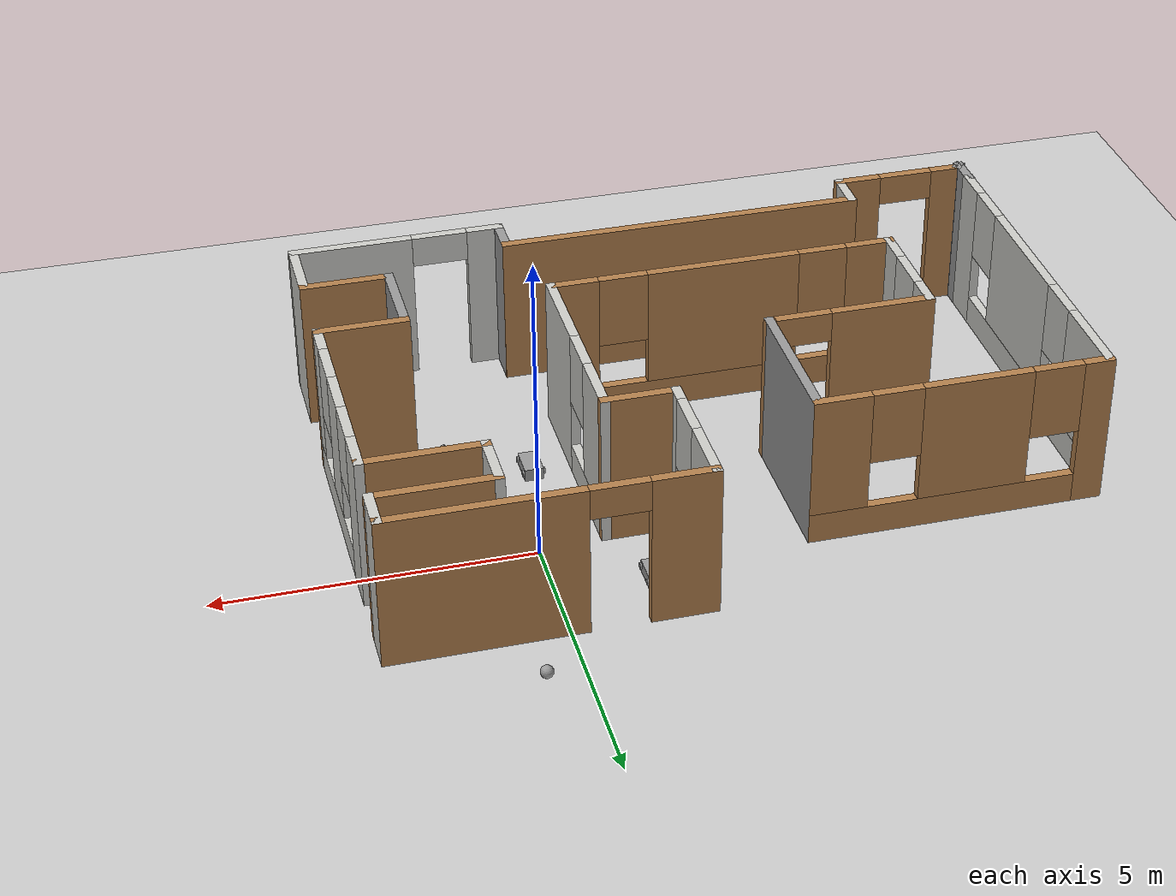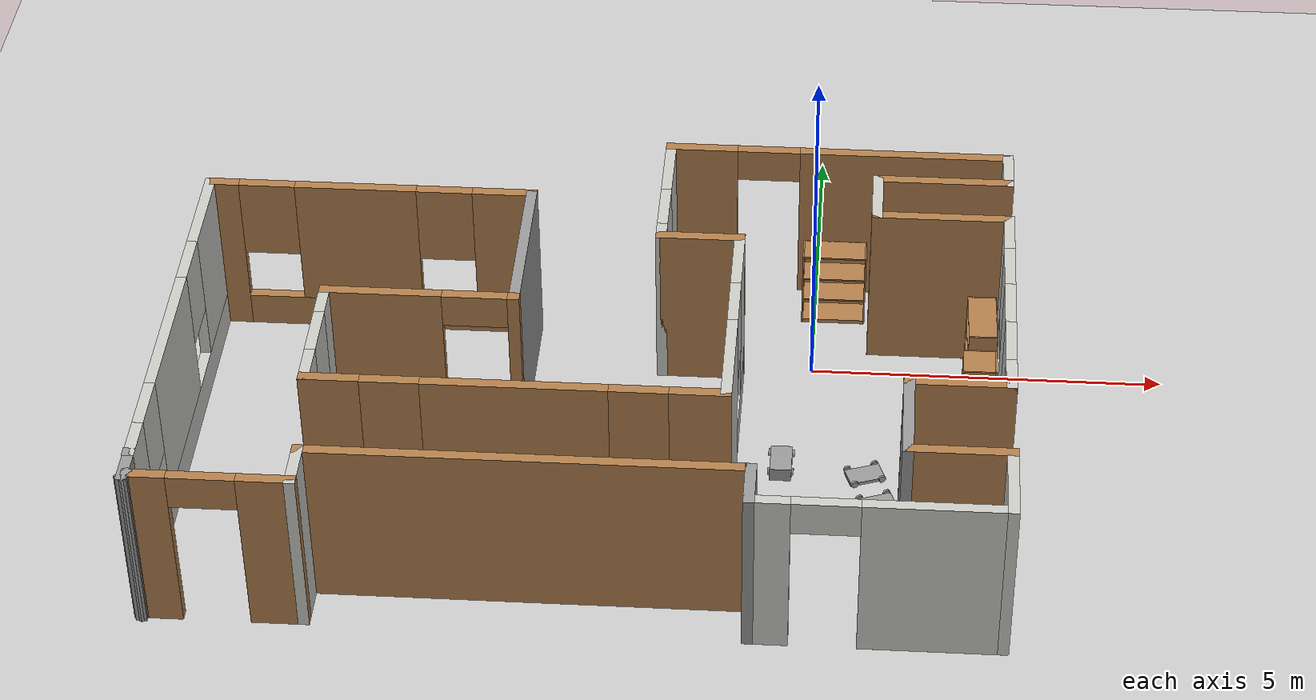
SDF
<sdf version="1.6">
 <world name="default">
  <plugin name="hello" filename="libhello.so"/>
  <light name="sun" type="directional">
   <pose>0 0 10 0 -0 0</pose>
   <diffuse>0.8 0.8 0.8 1</diffuse>
   <specular>0.2 0.2 0.2 1</specular>
   <attenuation>
    <range>1000</range>
    <constant>0.9</constant>
    <linear>0.01</linear>
    <quadratic>0.001</quadratic>
   </attenuation>
   <direction>-0.5 0.1 -0.9</direction>
  </light>
  <model name="ground_plane">
   <static>1</static>
   <link name="link">
    <collision name="collision">
     <geometry><plane><normal>0 0 1</normal><size>100 100</size></plane></geometry>
     <surface>
      <contact><collide_bitmask>65535</collide_bitmask></contact>
      <friction><ode><mu>100</mu><mu2>50</mu2></ode></friction>
     </surface>
    </collision>
    <visual name="visual">
     <cast_shadows>0</cast_shadows>
     <geometry><plane><normal>0 0 1</normal><size>100 100</size></plane></geometry>
     <material>
      <script><uri>file://media/materials/scripts/gazebo.material</uri><name>Gazebo/Grey</name></script>
     </material>
    </visual>
   </link>
  </model>
  <gravity>0 0 -9.8</gravity>
  <magnetic_field>6e-06 2.3e-05 -4.2e-05</magnetic_field>
  <atmosphere type="adiabatic"/>
  <physics name="default_physics" default="0" type="ode">
   <max_step_size>0.001</max_step_size>
   <real_time_factor>1</real_time_factor>
   <real_time_update_rate>1000</real_time_update_rate>
  </physics>
  <scene><ambient>0.4 0.4 0.4 1</ambient><background>0.7 0.7 0.7 1</background><shadows>1</shadows></scene>
  <spherical_coordinates>
   <surface_model>EARTH_WGS84</surface_model>
   <latitude_deg>0</latitude_deg>
   <longitude_deg>0</longitude_deg>
   <elevation>0</elevation>
   <heading_deg>0</heading_deg>
  </spherical_coordinates>
  <model name="building1">
   <pose>-2.98642 -1.84689 0 0 -0 0</pose>
   <link name="Wall_0">
    <collision name="Wall_0_Collision">
     <geometry><box><size>0.16 0.15 2.5</size></box></geometry>
     <pose>0 0 1.25 0 -0 0</pose>
    </collision>
    <visual name="Wall_0_Visual">
     <pose>0 0 1.25 0 -0 0</pose>
     <geometry><box><size>0.16 0.15 2.5</size></box></geometry>
     <material>
      <script><uri>file://media/materials/scripts/gazebo.material</uri><name>Gazebo/Grey</name></script>
      <ambient>1 1 1 1</ambient>
     </material>
     <meta><layer>0</layer></meta>
    </visual>
    <pose>-5.66464 -3.30521 0 0 -0 0</pose>
   </link>
   <link name="Wall_1">
    <pose>-5.65964 -0.380215 0 0 -0 1.5708</pose>
    <visual name="Wall_1_Visual_0">
     <pose>-2.67306 0 1.25 0 -0 0</pose>
     <geometry><box><size>0.653888 0.15 2.5</size></box></geometry>
     <material>
      <script><uri>file://media/materials/scripts/gazebo.material</uri><name>Gazebo/CeilingTiled</name></script>
      <ambient>1 1 1 1</ambient>
     </material>
     <meta><layer>0</layer></meta>
    </visual>
    <collision name="Wall_1_Collision_0">
     <geometry><box><size>0.653888 0.15 2.5</size></box></geometry>
     <pose>-2.67306 0 1.25 0 -0 0</pose>
    </collision>
    <visual name="Wall_1_Visual_1">
     <pose>0.326944 0 0.25 0 -0 0</pose>
     <geometry><box><size>5.34611 0.15 0.5</size></box></geometry>
     <material>
      <script><uri>file://media/materials/scripts/gazebo.material</uri><name>Gazebo/CeilingTiled</name></script>
      <ambient>1 1 1 1</ambient>
     </material>
     <meta><layer>0</layer></meta>
    </visual>
    <collision name="Wall_1_Collision_1">
     <geometry><box><size>5.34611 0.15 0.5</size></box></geometry>
     <pose>0.326944 0 0.25 0 -0 0</pose>
    </collision>
    <visual name="Wall_1_Visual_2">
     <pose>-0.416601 0 1.5 0 -0 0</pose>
     <geometry><box><size>2.25902 0.15 2</size></box></geometry>
     <material>
      <script><uri>file://media/materials/scripts/gazebo.material</uri><name>Gazebo/CeilingTiled</name></script>
      <ambient>1 1 1 1</ambient>
     </material>
     <meta><layer>0</layer></meta>
    </visual>
    <collision name="Wall_1_Collision_2">
     <geometry><box><size>2.25902 0.15 2</size></box></geometry>
     <pose>-0.416601 0 1.5 0 -0 0</pose>
    </collision>
    <visual name="Wall_1_Visual_3">
     <pose>2.25645 0 1.5 0 -0 0</pose>
     <geometry><box><size>1.48709 0.15 2</size></box></geometry>
     <material>
      <script><uri>file://media/materials/scripts/gazebo.material</uri><name>Gazebo/CeilingTiled</name></script>
      <ambient>1 1 1 1</ambient>
     </material>
     <meta><layer>0</layer></meta>
    </visual>
    <collision name="Wall_1_Collision_3">
     <geometry><box><size>1.48709 0.15 2</size></box></geometry>
     <pose>2.25645 0 1.5 0 -0 0</pose>
    </collision>
    <visual name="Wall_1_Visual_4">
     <pose>-1.94611 0 1.9 0 -0 0</pose>
     <geometry><box><size>0.8 0.15 1.2</size></box></geometry>
     <material>
      <script><uri>file://media/materials/scripts/gazebo.material</uri><name>Gazebo/CeilingTiled</name></script>
      <ambient>1 1 1 1</ambient>
     </material>
     <meta><layer>0</layer></meta>
    </visual>
    <collision name="Wall_1_Collision_4">
     <geometry><box><size>0.8 0.15 1.2</size></box></geometry>
     <pose>-1.94611 0 1.9 0 -0 0</pose>
    </collision>
    <visual name="Wall_1_Visual_5">
     <pose>1.11291 0 1.9 0 -0 0</pose>
     <geometry><box><size>0.8 0.15 1.2</size></box></geometry>
     <material>
      <script><uri>file://media/materials/scripts/gazebo.material</uri><name>Gazebo/CeilingTiled</name></script>
      <ambient>1 1 1 1</ambient>
     </material>
     <meta><layer>0</layer></meta>
    </visual>
    <collision name="Wall_1_Collision_5">
     <geometry><box><size>0.8 0.15 1.2</size></box></geometry>
     <pose>1.11291 0 1.9 0 -0 0</pose>
    </collision>
   </link>
   <link name="Wall_10">
    <pose>3.26536 3.79479 0 0 -0 0</pose>
    <visual name="Wall_10_Visual_0">
     <pose>-1.98107 0 1.25 0 -0 0</pose>
     <geometry><box><size>1.03787 0.15 2.5</size></box></geometry>
     <material>
      <script><uri>file://media/materials/scripts/gazebo.material</uri><name>Gazebo/Wood</name></script>
      <ambient>1 1 1 1</ambient>
     </material>
     <meta><layer>0</layer></meta>
    </visual>
    <collision name="Wall_10_Collision_0">
     <geometry><box><size>1.03787 0.15 2.5</size></box></geometry>
     <pose>-1.98107 0 1.25 0 -0 0</pose>
    </collision>
    <visual name="Wall_10_Visual_1">
     <pose>0.968935 0 1.25 0 -0 0</pose>
     <geometry><box><size>3.06213 0.15 2.5</size></box></geometry>
     <material>
      <script><uri>file://media/materials/scripts/gazebo.material</uri><name>Gazebo/Wood</name></script>
      <ambient>1 1 1 1</ambient>
     </material>
     <meta><layer>0</layer></meta>
    </visual>
    <collision name="Wall_10_Collision_1">
     <geometry><box><size>3.06213 0.15 2.5</size></box></geometry>
     <pose>0.968935 0 1.25 0 -0 0</pose>
    </collision>
    <visual name="Wall_10_Visual_2">
     <pose>-1.01213 0 2.25 0 -0 0</pose>
     <geometry><box><size>0.9 0.15 0.5</size></box></geometry>
     <material>
      <script><uri>file://media/materials/scripts/gazebo.material</uri><name>Gazebo/Wood</name></script>
      <ambient>1 1 1 1</ambient>
     </material>
     <meta><layer>0</layer></meta>
    </visual>
    <collision name="Wall_10_Collision_2">
     <geometry><box><size>0.9 0.15 0.5</size></box></geometry>
     <pose>-1.01213 0 2.25 0 -0 0</pose>
    </collision>
   </link>
   <link name="Wall_11">
    <collision name="Wall_11_Collision">
     <geometry><box><size>0.75 0.15 2.5</size></box></geometry>
     <pose>0 0 1.25 0 -0 0</pose>
    </collision>
    <visual name="Wall_11_Visual">
     <pose>0 0 1.25 0 -0 0</pose>
     <geometry><box><size>0.75 0.15 2.5</size></box></geometry>
     <material>
      <script><uri>file://media/materials/scripts/gazebo.material</uri><name>Gazebo/CeilingTiled</name></script>
      <ambient>1 1 1 1</ambient>
     </material>
     <meta><layer>0</layer></meta>
    </visual>
    <pose>5.69036 3.49478 0 0 0 -1.5708</pose>
   </link>
   <link name="Wall_12">
    <collision name="Wall_12_Collision">
     <geometry><box><size>2 0.15 2.5</size></box></geometry>
     <pose>0 0 1.25 0 -0 0</pose>
    </collision>
    <visual name="Wall_12_Visual">
     <pose>0 0 1.25 0 -0 0</pose>
     <geometry><box><size>2 0.15 2.5</size></box></geometry>
     <material>
      <script><uri>file://media/materials/scripts/gazebo.material</uri><name>Gazebo/Wood</name></script>
      <ambient>1 1 1 1</ambient>
     </material>
     <meta><layer>0</layer></meta>
    </visual>
    <pose>4.76536 3.19478 0 0 -0 3.14159</pose>
   </link>
   <link name="Wall_13">
    <collision name="Wall_13_Collision">
     <geometry><box><size>1 0.15 2.5</size></box></geometry>
     <pose>0 0 1.25 0 -0 0</pose>
    </collision>
    <visual name="Wall_13_Visual">
     <pose>0 0 1.25 0 -0 0</pose>
     <geometry><box><size>1 0.15 2.5</size></box></geometry>
     <material>
      <script><uri>file://media/materials/scripts/gazebo.material</uri><name>Gazebo/CeilingTiled</name></script>
      <ambient>1 1 1 1</ambient>
     </material>
     <meta><layer>0</layer></meta>
    </visual>
    <pose>3.84036 2.76979 0 0 0 -1.5708</pose>
   </link>
   <link name="Wall_14">
    <collision name="Wall_14_Collision">
     <geometry><box><size>2 0.15 2.5</size></box></geometry>
     <pose>0 0 1.25 0 -0 0</pose>
    </collision>
    <visual name="Wall_14_Visual">
     <pose>0 0 1.25 0 -0 0</pose>
     <geometry><box><size>2 0.15 2.5</size></box></geometry>
     <material>
      <script><uri>file://media/materials/scripts/gazebo.material</uri><name>Gazebo/Wood</name></script>
      <ambient>1 1 1 1</ambient>
     </material>
     <meta><layer>0</layer></meta>
    </visual>
    <pose>4.76536 2.34478 0 0 -0 0</pose>
   </link>
   <link name="Wall_15">
    <pose>5.69036 0.544785 0 0 0 -1.5708</pose>
    <visual name="Wall_15_Visual_0">
     <pose>-1.50677 0 1.25 0 -0 0</pose>
     <geometry><box><size>0.736466 0.15 2.5</size></box></geometry>
     <material>
      <script><uri>file://media/materials/scripts/gazebo.material</uri><name>Gazebo/CeilingTiled</name></script>
      <ambient>1 1 1 1</ambient>
     </material>
     <meta><layer>0</layer></meta>
    </visual>
    <collision name="Wall_15_Collision_0">
     <geometry><box><size>0.736466 0.15 2.5</size></box></geometry>
     <pose>-1.50677 0 1.25 0 -0 0</pose>
    </collision>
    <visual name="Wall_15_Visual_1">
     <pose>0.368233 0 0.25 0 -0 0</pose>
     <geometry><box><size>3.01353 0.15 0.5</size></box></geometry>
     <material>
      <script><uri>file://media/materials/scripts/gazebo.material</uri><name>Gazebo/CeilingTiled</name></script>
      <ambient>1 1 1 1</ambient>
     </material>
     <meta><layer>0</layer></meta>
    </visual>
    <collision name="Wall_15_Collision_1">
     <geometry><box><size>3.01353 0.15 0.5</size></box></geometry>
     <pose>0.368233 0 0.25 0 -0 0</pose>
    </collision>
    <visual name="Wall_15_Visual_2">
     <pose>0.072107 0 1.5 0 -0 0</pose>
     <geometry><box><size>0.821282 0.15 2</size></box></geometry>
     <material>
      <script><uri>file://media/materials/scripts/gazebo.material</uri><name>Gazebo/CeilingTiled</name></script>
      <ambient>1 1 1 1</ambient>
     </material>
     <meta><layer>0</layer></meta>
    </visual>
    <collision name="Wall_15_Collision_2">
     <geometry><box><size>0.821282 0.15 2</size></box></geometry>
     <pose>0.072107 0 1.5 0 -0 0</pose>
    </collision>
    <visual name="Wall_15_Visual_3">
     <pose>1.57887 0 1.5 0 -0 0</pose>
     <geometry><box><size>0.592252 0.15 2</size></box></geometry>
     <material>
      <script><uri>file://media/materials/scripts/gazebo.material</uri><name>Gazebo/CeilingTiled</name></script>
      <ambient>1 1 1 1</ambient>
     </material>
     <meta><layer>0</layer></meta>
    </visual>
    <collision name="Wall_15_Collision_3">
     <geometry><box><size>0.592252 0.15 2</size></box></geometry>
     <pose>1.57887 0 1.5 0 -0 0</pose>
    </collision>
    <visual name="Wall_15_Visual_4">
     <pose>-0.738534 0 1.9 0 -0 0</pose>
     <geometry><box><size>0.8 0.15 1.2</size></box></geometry>
     <material>
      <script><uri>file://media/materials/scripts/gazebo.material</uri><name>Gazebo/CeilingTiled</name></script>
      <ambient>1 1 1 1</ambient>
     </material>
     <meta><layer>0</layer></meta>
    </visual>
    <collision name="Wall_15_Collision_4">
     <geometry><box><size>0.8 0.15 1.2</size></box></geometry>
     <pose>-0.738534 0 1.9 0 -0 0</pose>
    </collision>
    <visual name="Wall_15_Visual_5">
     <pose>0.882748 0 1.9 0 -0 0</pose>
     <geometry><box><size>0.8 0.15 1.2</size></box></geometry>
     <material>
      <script><uri>file://media/materials/scripts/gazebo.material</uri><name>Gazebo/CeilingTiled</name></script>
      <ambient>1 1 1 1</ambient>
     </material>
     <meta><layer>0</layer></meta>
    </visual>
    <collision name="Wall_15_Collision_5">
     <geometry><box><size>0.8 0.15 1.2</size></box></geometry>
     <pose>0.882748 0 1.9 0 -0 0</pose>
    </collision>
   </link>
   <link name="Wall_16">
    <collision name="Wall_16_Collision">
     <geometry><box><size>1.5 0.15 2.5</size></box></geometry>
     <pose>0 0 1.25 0 -0 0</pose>
    </collision>
    <visual name="Wall_16_Visual">
     <pose>0 0 1.25 0 -0 0</pose>
     <geometry><box><size>1.5 0.15 2.5</size></box></geometry>
     <material>
      <script><uri>file://media/materials/scripts/gazebo.material</uri><name>Gazebo/Wood</name></script>
      <ambient>1 1 1 1</ambient>
     </material>
     <meta><layer>0</layer></meta>
    </visual>
    <pose>5.01536 -1.25521 0 0 -0 3.14159</pose>
   </link>
   <link name="Wall_17">
    <collision name="Wall_17_Collision">
     <geometry><box><size>1.5 0.15 2.5</size></box></geometry>
     <pose>0 0 1.25 0 -0 0</pose>
    </collision>
    <visual name="Wall_17_Visual">
     <pose>0 0 1.25 0 -0 0</pose>
     <geometry><box><size>1.5 0.15 2.5</size></box></geometry>
     <material>
      <script><uri>file://media/materials/scripts/gazebo.material</uri><name>Gazebo/Grey</name></script>
      <ambient>1 1 1 1</ambient>
     </material>
     <meta><layer>0</layer></meta>
    </visual>
    <pose>4.34036 -1.93022 0 0 0 -1.5708</pose>
   </link>
   <link name="Wall_18">
    <collision name="Wall_18_Collision">
     <geometry><box><size>1.5 0.15 2.5</size></box></geometry>
     <pose>0 0 1.25 0 -0 0</pose>
    </collision>
    <visual name="Wall_18_Visual">
     <pose>0 0 1.25 0 -0 0</pose>
     <geometry><box><size>1.5 0.15 2.5</size></box></geometry>
     <material>
      <script><uri>file://media/materials/scripts/gazebo.material</uri><name>Gazebo/Wood</name></script>
      <ambient>1 1 1 1</ambient>
     </material>
     <meta><layer>0</layer></meta>
    </visual>
    <pose>5.01536 -2.60521 0 0 -0 0</pose>
   </link>
   <link name="Wall_19">
    <collision name="Wall_19_Collision">
     <geometry><box><size>1.25 0.15 2.5</size></box></geometry>
     <pose>0 0 1.25 0 -0 0</pose>
    </collision>
    <visual name="Wall_19_Visual">
     <pose>0 0 1.25 0 -0 0</pose>
     <geometry><box><size>1.25 0.15 2.5</size></box></geometry>
     <material>
      <script><uri>file://media/materials/scripts/gazebo.material</uri><name>Gazebo/CeilingTiled</name></script>
      <ambient>1 1 1 1</ambient>
     </material>
     <meta><layer>0</layer></meta>
    </visual>
    <pose>5.69036 -3.15522 0 0 0 -1.5708</pose>
   </link>
   <link name="Wall_2">
    <pose>-3.35964 2.54479 0 0 -0 0</pose>
    <visual name="Wall_2_Visual_0">
     <pose>-2.12953 0 1.25 0 -0 0</pose>
     <geometry><box><size>0.490936 0.15 2.5</size></box></geometry>
     <material>
      <script><uri>file://media/materials/scripts/gazebo.material</uri><name>Gazebo/Wood</name></script>
      <ambient>1 1 1 1</ambient>
     </material>
     <meta><layer>0</layer></meta>
    </visual>
    <collision name="Wall_2_Collision_0">
     <geometry><box><size>0.490936 0.15 2.5</size></box></geometry>
     <pose>-2.12953 0 1.25 0 -0 0</pose>
    </collision>
    <visual name="Wall_2_Visual_1">
     <pose>0.245468 0 0.25 0 -0 0</pose>
     <geometry><box><size>4.25906 0.15 0.5</size></box></geometry>
     <material>
      <script><uri>file://media/materials/scripts/gazebo.material</uri><name>Gazebo/Wood</name></script>
      <ambient>1 1 1 1</ambient>
     </material>
     <meta><layer>0</layer></meta>
    </visual>
    <collision name="Wall_2_Collision_1">
     <geometry><box><size>4.25906 0.15 0.5</size></box></geometry>
     <pose>0.245468 0 0.25 0 -0 0</pose>
    </collision>
    <visual name="Wall_2_Visual_2">
     <pose>-0.21457 0 1.5 0 -0 0</pose>
     <geometry><box><size>1.73899 0.15 2</size></box></geometry>
     <material>
      <script><uri>file://media/materials/scripts/gazebo.material</uri><name>Gazebo/Wood</name></script>
      <ambient>1 1 1 1</ambient>
     </material>
     <meta><layer>0</layer></meta>
    </visual>
    <collision name="Wall_2_Collision_2">
     <geometry><box><size>1.73899 0.15 2</size></box></geometry>
     <pose>-0.21457 0 1.5 0 -0 0</pose>
    </collision>
    <visual name="Wall_2_Visual_3">
     <pose>1.91496 0 1.5 0 -0 0</pose>
     <geometry><box><size>0.920075 0.15 2</size></box></geometry>
     <material>
      <script><uri>file://media/materials/scripts/gazebo.material</uri><name>Gazebo/Wood</name></script>
      <ambient>1 1 1 1</ambient>
     </material>
     <meta><layer>0</layer></meta>
    </visual>
    <collision name="Wall_2_Collision_3">
     <geometry><box><size>0.920075 0.15 2</size></box></geometry>
     <pose>1.91496 0 1.5 0 -0 0</pose>
    </collision>
    <visual name="Wall_2_Visual_4">
     <pose>-1.48406 0 1.9 0 -0 0</pose>
     <geometry><box><size>0.8 0.15 1.2</size></box></geometry>
     <material>
      <script><uri>file://media/materials/scripts/gazebo.material</uri><name>Gazebo/Wood</name></script>
      <ambient>1 1 1 1</ambient>
     </material>
     <meta><layer>0</layer></meta>
    </visual>
    <collision name="Wall_2_Collision_4">
     <geometry><box><size>0.8 0.15 1.2</size></box></geometry>
     <pose>-1.48406 0 1.9 0 -0 0</pose>
    </collision>
    <visual name="Wall_2_Visual_5">
     <pose>1.05492 0 1.9 0 -0 0</pose>
     <geometry><box><size>0.8 0.15 1.2</size></box></geometry>
     <material>
      <script><uri>file://media/materials/scripts/gazebo.material</uri><name>Gazebo/Wood</name></script>
      <ambient>1 1 1 1</ambient>
     </material>
     <meta><layer>0</layer></meta>
    </visual>
    <collision name="Wall_2_Collision_5">
     <geometry><box><size>0.8 0.15 1.2</size></box></geometry>
     <pose>1.05492 0 1.9 0 -0 0</pose>
    </collision>
   </link>
   <link name="Wall_20">
    <pose>4.01536 -3.70521 0 0 -0 3.14159</pose>
    <visual name="Wall_20_Visual_0">
     <pose>-0.754264 0 1.25 0 -0 0</pose>
     <geometry><box><size>1.99147 0.15 2.5</size></box></geometry>
     <material>
      <script><uri>file://media/materials/scripts/gazebo.material</uri><name>Gazebo/CeilingTiled</name></script>
      <ambient>1 1 1 1</ambient>
     </material>
     <meta><layer>0</layer></meta>
    </visual>
    <collision name="Wall_20_Collision_0">
     <geometry><box><size>1.99147 0.15 2.5</size></box></geometry>
     <pose>-0.754264 0 1.25 0 -0 0</pose>
    </collision>
    <visual name="Wall_20_Visual_1">
     <pose>1.44574 0 1.25 0 -0 0</pose>
     <geometry><box><size>0.608527 0.15 2.5</size></box></geometry>
     <material>
      <script><uri>file://media/materials/scripts/gazebo.material</uri><name>Gazebo/CeilingTiled</name></script>
      <ambient>1 1 1 1</ambient>
     </material>
     <meta><layer>0</layer></meta>
    </visual>
    <collision name="Wall_20_Collision_1">
     <geometry><box><size>0.608527 0.15 2.5</size></box></geometry>
     <pose>1.44574 0 1.25 0 -0 0</pose>
    </collision>
    <visual name="Wall_20_Visual_2">
     <pose>0.691473 0 2.25 0 -0 0</pose>
     <geometry><box><size>0.9 0.15 0.5</size></box></geometry>
     <material>
      <script><uri>file://media/materials/scripts/gazebo.material</uri><name>Gazebo/CeilingTiled</name></script>
      <ambient>1 1 1 1</ambient>
     </material>
     <meta><layer>0</layer></meta>
    </visual>
    <collision name="Wall_20_Collision_2">
     <geometry><box><size>0.9 0.15 0.5</size></box></geometry>
     <pose>0.691473 0 2.25 0 -0 0</pose>
    </collision>
   </link>
   <link name="Wall_21">
    <collision name="Wall_21_Collision">
     <geometry><box><size>0.75 0.15 2.5</size></box></geometry>
     <pose>0 0 1.25 0 -0 0</pose>
    </collision>
    <visual name="Wall_21_Visual">
     <pose>0 0 1.25 0 -0 0</pose>
     <geometry><box><size>0.75 0.15 2.5</size></box></geometry>
     <material>
      <script><uri>file://media/materials/scripts/gazebo.material</uri><name>Gazebo/Grey</name></script>
      <ambient>1 1 1 1</ambient>
     </material>
     <meta><layer>0</layer></meta>
    </visual>
    <pose>2.34036 -3.40522 0 0 -0 1.5708</pose>
   </link>
   <link name="Wall_22">
    <collision name="Wall_22_Collision">
     <geometry><box><size>6 0.15 2.5</size></box></geometry>
     <pose>0 0 1.25 0 -0 0</pose>
    </collision>
    <visual name="Wall_22_Visual">
     <pose>0 0 1.25 0 -0 0</pose>
     <geometry><box><size>6 0.15 2.5</size></box></geometry>
     <material>
      <script><uri>file://media/materials/scripts/gazebo.material</uri><name>Gazebo/Wood</name></script>
      <ambient>1 0.764706 0.305882 1</ambient>
     </material>
     <meta><layer>0</layer></meta>
    </visual>
    <pose>-0.584642 -3.10521 0 0 -0 3.14159</pose>
   </link>
   <link name="Wall_23">
    <collision name="Wall_23_Collision">
     <geometry><box><size>0.75 0.15 2.5</size></box></geometry>
     <pose>0 0 1.25 0 -0 0</pose>
    </collision>
    <visual name="Wall_23_Visual">
     <pose>0 0 1.25 0 -0 0</pose>
     <geometry><box><size>0.75 0.15 2.5</size></box></geometry>
     <material>
      <script><uri>file://media/materials/scripts/gazebo.material</uri><name>Gazebo/CeilingTiled</name></script>
      <ambient>1 1 1 1</ambient>
     </material>
     <meta><layer>0</layer></meta>
    </visual>
    <pose>-3.50964 -3.40522 0 0 0 -1.5708</pose>
   </link>
   <link name="Wall_24">
    <pose>-4.55964 -3.70521 0 0 -0 3.14159</pose>
    <visual name="Wall_24_Visual_0">
     <pose>-0.737239 0 1.25 0 -0 0</pose>
     <geometry><box><size>0.775523 0.15 2.5</size></box></geometry>
     <material>
      <script><uri>file://media/materials/scripts/gazebo.material</uri><name>Gazebo/Wood</name></script>
      <ambient>1 1 1 1</ambient>
     </material>
     <meta><layer>0</layer></meta>
    </visual>
    <collision name="Wall_24_Collision_0">
     <geometry><box><size>0.775523 0.15 2.5</size></box></geometry>
     <pose>-0.737239 0 1.25 0 -0 0</pose>
    </collision>
    <visual name="Wall_24_Visual_1">
     <pose>0.837761 0 1.25 0 -0 0</pose>
     <geometry><box><size>0.574477 0.15 2.5</size></box></geometry>
     <material>
      <script><uri>file://media/materials/scripts/gazebo.material</uri><name>Gazebo/Wood</name></script>
      <ambient>1 1 1 1</ambient>
     </material>
     <meta><layer>0</layer></meta>
    </visual>
    <collision name="Wall_24_Collision_1">
     <geometry><box><size>0.574477 0.15 2.5</size></box></geometry>
     <pose>0.837761 0 1.25 0 -0 0</pose>
    </collision>
    <visual name="Wall_24_Visual_2">
     <pose>0.100523 0 2.25 0 -0 0</pose>
     <geometry><box><size>0.9 0.15 0.5</size></box></geometry>
     <material>
      <script><uri>file://media/materials/scripts/gazebo.material</uri><name>Gazebo/Wood</name></script>
      <ambient>1 1 1 1</ambient>
     </material>
     <meta><layer>0</layer></meta>
    </visual>
    <collision name="Wall_24_Collision_2">
     <geometry><box><size>0.9 0.15 0.5</size></box></geometry>
     <pose>0.100523 0 2.25 0 -0 0</pose>
    </collision>
   </link>
   <link name="Wall_27">
    <collision name="Wall_27_Collision">
     <geometry><box><size>0.227225 0.15 2.5</size></box></geometry>
     <pose>0 0 1.25 0 -0 0</pose>
    </collision>
    <visual name="Wall_27_Visual">
     <pose>0 0 1.25 0 -0 0</pose>
     <geometry><box><size>0.227225 0.15 2.5</size></box></geometry>
     <material>
      <script><uri>file://media/materials/scripts/gazebo.material</uri><name>Gazebo/Grey</name></script>
      <ambient>1 1 1 1</ambient>
     </material>
     <meta><layer>0</layer></meta>
    </visual>
    <pose>-5.63464 -3.73464 0 0 0 -2.27504</pose>
   </link>
   <link name="Wall_28">
    <collision name="Wall_28_Collision">
     <geometry><box><size>0.608853 0.15 2.5</size></box></geometry>
     <pose>0 0 1.25 0 -0 0</pose>
    </collision>
    <visual name="Wall_28_Visual">
     <pose>0 0 1.25 0 -0 0</pose>
     <geometry><box><size>0.608853 0.15 2.5</size></box></geometry>
     <material>
      <script><uri>file://media/materials/scripts/gazebo.material</uri><name>Gazebo/Grey</name></script>
      <ambient>1 1 1 1</ambient>
     </material>
     <meta><layer>0</layer></meta>
    </visual>
    <pose>-5.65964 -3.53464 0 0 -0 1.5708</pose>
   </link>
   <link name="Wall_3">
    <collision name="Wall_3_Collision">
     <geometry><box><size>2.5 0.15 2.5</size></box></geometry>
     <pose>0 0 1.25 0 -0 0</pose>
    </collision>
    <visual name="Wall_3_Visual">
     <pose>0 0 1.25 0 -0 0</pose>
     <geometry><box><size>2.5 0.15 2.5</size></box></geometry>
     <material>
      <script><uri>file://media/materials/scripts/gazebo.material</uri><name>Gazebo/Grey</name></script>
      <ambient>1 1 1 1</ambient>
     </material>
     <meta><layer>0</layer></meta>
    </visual>
    <pose>-1.05964 1.36979 0 0 0 -1.5708</pose>
   </link>
   <link name="Wall_4">
    <pose>-2.35964 0.194785 0 0 -0 3.14159</pose>
    <visual name="Wall_4_Visual_0">
     <pose>-1.29175 0 1.25 0 -0 0</pose>
     <geometry><box><size>0.1665 0.15 2.5</size></box></geometry>
     <material>
      <script><uri>file://media/materials/scripts/gazebo.material</uri><name>Gazebo/Wood</name></script>
      <ambient>1 1 1 1</ambient>
     </material>
     <meta><layer>0</layer></meta>
    </visual>
    <collision name="Wall_4_Collision_0">
     <geometry><box><size>0.1665 0.15 2.5</size></box></geometry>
     <pose>-1.29175 0 1.25 0 -0 0</pose>
    </collision>
    <visual name="Wall_4_Visual_1">
     <pose>0.53325 0 1.25 0 -0 0</pose>
     <geometry><box><size>1.6835 0.15 2.5</size></box></geometry>
     <material>
      <script><uri>file://media/materials/scripts/gazebo.material</uri><name>Gazebo/Wood</name></script>
      <ambient>1 1 1 1</ambient>
     </material>
     <meta><layer>0</layer></meta>
    </visual>
    <collision name="Wall_4_Collision_1">
     <geometry><box><size>1.6835 0.15 2.5</size></box></geometry>
     <pose>0.53325 0 1.25 0 -0 0</pose>
    </collision>
    <visual name="Wall_4_Visual_2">
     <pose>-0.7585 0 2.25 0 -0 0</pose>
     <geometry><box><size>0.9 0.15 0.5</size></box></geometry>
     <material>
      <script><uri>file://media/materials/scripts/gazebo.material</uri><name>Gazebo/Wood</name></script>
      <ambient>1 1 1 1</ambient>
     </material>
     <meta><layer>0</layer></meta>
    </visual>
    <collision name="Wall_4_Collision_2">
     <geometry><box><size>0.9 0.15 0.5</size></box></geometry>
     <pose>-0.7585 0 2.25 0 -0 0</pose>
    </collision>
   </link>
   <link name="Wall_5">
    <pose>-3.65964 -0.730215 0 0 0 -1.5708</pose>
    <visual name="Wall_5_Visual_0">
     <pose>-0.712585 0 1.25 0 -0 0</pose>
     <geometry><box><size>0.574831 0.15 2.5</size></box></geometry>
     <material>
      <script><uri>file://media/materials/scripts/gazebo.material</uri><name>Gazebo/CeilingTiled</name></script>
      <ambient>1 1 1 1</ambient>
     </material>
     <meta><layer>0</layer></meta>
    </visual>
    <collision name="Wall_5_Collision_0">
     <geometry><box><size>0.574831 0.15 2.5</size></box></geometry>
     <pose>-0.712585 0 1.25 0 -0 0</pose>
    </collision>
    <visual name="Wall_5_Visual_1">
     <pose>0.287415 0 0.25 0 -0 0</pose>
     <geometry><box><size>1.42517 0.15 0.5</size></box></geometry>
     <material>
      <script><uri>file://media/materials/scripts/gazebo.material</uri><name>Gazebo/CeilingTiled</name></script>
      <ambient>1 1 1 1</ambient>
     </material>
     <meta><layer>0</layer></meta>
    </visual>
    <collision name="Wall_5_Collision_1">
     <geometry><box><size>1.42517 0.15 0.5</size></box></geometry>
     <pose>0.287415 0 0.25 0 -0 0</pose>
    </collision>
    <visual name="Wall_5_Visual_2">
     <pose>0.687415 0 1.5 0 -0 0</pose>
     <geometry><box><size>0.625169 0.15 2</size></box></geometry>
     <material>
      <script><uri>file://media/materials/scripts/gazebo.material</uri><name>Gazebo/CeilingTiled</name></script>
      <ambient>1 1 1 1</ambient>
     </material>
     <meta><layer>0</layer></meta>
    </visual>
    <collision name="Wall_5_Collision_2">
     <geometry><box><size>0.625169 0.15 2</size></box></geometry>
     <pose>0.687415 0 1.5 0 -0 0</pose>
    </collision>
    <visual name="Wall_5_Visual_3">
     <pose>-0.025169 0 1.9 0 -0 0</pose>
     <geometry><box><size>0.8 0.15 1.2</size></box></geometry>
     <material>
      <script><uri>file://media/materials/scripts/gazebo.material</uri><name>Gazebo/CeilingTiled</name></script>
      <ambient>1 1 1 1</ambient>
     </material>
     <meta><layer>0</layer></meta>
    </visual>
    <collision name="Wall_5_Collision_3">
     <geometry><box><size>0.8 0.15 1.2</size></box></geometry>
     <pose>-0.025169 0 1.9 0 -0 0</pose>
    </collision>
   </link>
   <link name="Wall_6">
    <pose>-0.859642 -1.65522 0 0 -0 0</pose>
    <visual name="Wall_6_Visual_0">
     <pose>-2.4671 0 1.25 0 -0 0</pose>
     <geometry><box><size>0.815794 0.15 2.5</size></box></geometry>
     <material>
      <script><uri>file://media/materials/scripts/gazebo.material</uri><name>Gazebo/Wood</name></script>
      <ambient>0.996078 0.47451 0.0196078 1</ambient>
     </material>
     <meta><layer>0</layer></meta>
    </visual>
    <collision name="Wall_6_Collision_0">
     <geometry><box><size>0.815794 0.15 2.5</size></box></geometry>
     <pose>-2.4671 0 1.25 0 -0 0</pose>
    </collision>
    <visual name="Wall_6_Visual_1">
     <pose>0.407897 0 0.25 0 -0 0</pose>
     <geometry><box><size>4.93421 0.15 0.5</size></box></geometry>
     <material>
      <script><uri>file://media/materials/scripts/gazebo.material</uri><name>Gazebo/Wood</name></script>
      <ambient>0.996078 0.47451 0.0196078 1</ambient>
     </material>
     <meta><layer>0</layer></meta>
    </visual>
    <collision name="Wall_6_Collision_1">
     <geometry><box><size>4.93421 0.15 0.5</size></box></geometry>
     <pose>0.407897 0 0.25 0 -0 0</pose>
    </collision>
    <visual name="Wall_6_Visual_2">
     <pose>-0.007334 0 1.5 0 -0 0</pose>
     <geometry><box><size>2.50374 0.15 2</size></box></geometry>
     <material>
      <script><uri>file://media/materials/scripts/gazebo.material</uri><name>Gazebo/Wood</name></script>
      <ambient>0.996078 0.47451 0.0196078 1</ambient>
     </material>
     <meta><layer>0</layer></meta>
    </visual>
    <collision name="Wall_6_Collision_2">
     <geometry><box><size>2.50374 0.15 2</size></box></geometry>
     <pose>-0.007334 0 1.5 0 -0 0</pose>
    </collision>
    <visual name="Wall_6_Visual_3">
     <pose>2.45977 0 1.5 0 -0 0</pose>
     <geometry><box><size>0.830462 0.15 2</size></box></geometry>
     <material>
      <script><uri>file://media/materials/scripts/gazebo.material</uri><name>Gazebo/Wood</name></script>
      <ambient>0.996078 0.47451 0.0196078 1</ambient>
     </material>
     <meta><layer>0</layer></meta>
    </visual>
    <collision name="Wall_6_Collision_3">
     <geometry><box><size>0.830462 0.15 2</size></box></geometry>
     <pose>2.45977 0 1.5 0 -0 0</pose>
    </collision>
    <visual name="Wall_6_Visual_4">
     <pose>-1.65921 0 1.9 0 -0 0</pose>
     <geometry><box><size>0.8 0.15 1.2</size></box></geometry>
     <material>
      <script><uri>file://media/materials/scripts/gazebo.material</uri><name>Gazebo/Wood</name></script>
      <ambient>0.996078 0.47451 0.0196078 1</ambient>
     </material>
     <meta><layer>0</layer></meta>
    </visual>
    <collision name="Wall_6_Collision_4">
     <geometry><box><size>0.8 0.15 1.2</size></box></geometry>
     <pose>-1.65921 0 1.9 0 -0 0</pose>
    </collision>
    <visual name="Wall_6_Visual_5">
     <pose>1.64454 0 1.9 0 -0 0</pose>
     <geometry><box><size>0.8 0.15 1.2</size></box></geometry>
     <material>
      <script><uri>file://media/materials/scripts/gazebo.material</uri><name>Gazebo/Wood</name></script>
      <ambient>0.996078 0.47451 0.0196078 1</ambient>
     </material>
     <meta><layer>0</layer></meta>
    </visual>
    <collision name="Wall_6_Collision_5">
     <geometry><box><size>0.8 0.15 1.2</size></box></geometry>
     <pose>1.64454 0 1.9 0 -0 0</pose>
    </collision>
   </link>
   <link name="Wall_7">
    <pose>1.94036 0.019785 0 0 -0 1.5708</pose>
    <visual name="Wall_7_Visual_0">
     <pose>-0.947972 0 1.25 0 -0 0</pose>
     <geometry><box><size>1.60406 0.15 2.5</size></box></geometry>
     <material>
      <script><uri>file://media/materials/scripts/gazebo.material</uri><name>Gazebo/CeilingTiled</name></script>
      <ambient>1 1 1 1</ambient>
     </material>
     <meta><layer>0</layer></meta>
    </visual>
    <collision name="Wall_7_Collision_0">
     <geometry><box><size>1.60406 0.15 2.5</size></box></geometry>
     <pose>-0.947972 0 1.25 0 -0 0</pose>
    </collision>
    <visual name="Wall_7_Visual_1">
     <pose>0.802028 0 0.25 0 -0 0</pose>
     <geometry><box><size>1.89594 0.15 0.5</size></box></geometry>
     <material>
      <script><uri>file://media/materials/scripts/gazebo.material</uri><name>Gazebo/CeilingTiled</name></script>
      <ambient>1 1 1 1</ambient>
     </material>
     <meta><layer>0</layer></meta>
    </visual>
    <collision name="Wall_7_Collision_1">
     <geometry><box><size>1.89594 0.15 0.5</size></box></geometry>
     <pose>0.802028 0 0.25 0 -0 0</pose>
    </collision>
    <visual name="Wall_7_Visual_2">
     <pose>1.20203 0 1.5 0 -0 0</pose>
     <geometry><box><size>1.09594 0.15 2</size></box></geometry>
     <material>
      <script><uri>file://media/materials/scripts/gazebo.material</uri><name>Gazebo/CeilingTiled</name></script>
      <ambient>1 1 1 1</ambient>
     </material>
     <meta><layer>0</layer></meta>
    </visual>
    <collision name="Wall_7_Collision_2">
     <geometry><box><size>1.09594 0.15 2</size></box></geometry>
     <pose>1.20203 0 1.5 0 -0 0</pose>
    </collision>
    <visual name="Wall_7_Visual_3">
     <pose>0.254057 0 1.9 0 -0 0</pose>
     <geometry><box><size>0.8 0.15 1.2</size></box></geometry>
     <material>
      <script><uri>file://media/materials/scripts/gazebo.material</uri><name>Gazebo/CeilingTiled</name></script>
      <ambient>1 1 1 1</ambient>
     </material>
     <meta><layer>0</layer></meta>
    </visual>
    <collision name="Wall_7_Collision_3">
     <geometry><box><size>0.8 0.15 1.2</size></box></geometry>
     <pose>0.254057 0 1.9 0 -0 0</pose>
    </collision>
   </link>
   <link name="Wall_8">
    <collision name="Wall_8_Collision">
     <geometry><box><size>1.25 0.15 2.5</size></box></geometry>
     <pose>0 0 1.25 0 -0 0</pose>
    </collision>
    <visual name="Wall_8_Visual">
     <pose>0 0 1.25 0 -0 0</pose>
     <geometry><box><size>1.25 0.15 2.5</size></box></geometry>
     <material>
      <script><uri>file://media/materials/scripts/gazebo.material</uri><name>Gazebo/Wood</name></script>
      <ambient>1 1 1 1</ambient>
     </material>
     <meta><layer>0</layer></meta>
    </visual>
    <pose>1.39036 1.69478 0 0 -0 3.14159</pose>
   </link>
   <link name="Wall_9">
    <pose>0.840358 2.74478 0 0 -0 1.5708</pose>
    <visual name="Wall_9_Visual_0">
     <pose>-0.957904 0 1.25 0 -0 0</pose>
     <geometry><box><size>0.334192 0.15 2.5</size></box></geometry>
     <material>
      <script><uri>file://media/materials/scripts/gazebo.material</uri><name>Gazebo/CeilingTiled</name></script>
      <ambient>1 1 1 1</ambient>
     </material>
     <meta><layer>0</layer></meta>
    </visual>
    <collision name="Wall_9_Collision_0">
     <geometry><box><size>0.334192 0.15 2.5</size></box></geometry>
     <pose>-0.957904 0 1.25 0 -0 0</pose>
    </collision>
    <visual name="Wall_9_Visual_1">
     <pose>0.167096 0 0.25 0 -0 0</pose>
     <geometry><box><size>1.91581 0.15 0.5</size></box></geometry>
     <material>
      <script><uri>file://media/materials/scripts/gazebo.material</uri><name>Gazebo/CeilingTiled</name></script>
      <ambient>1 1 1 1</ambient>
     </material>
     <meta><layer>0</layer></meta>
    </visual>
    <collision name="Wall_9_Collision_1">
     <geometry><box><size>1.91581 0.15 0.5</size></box></geometry>
     <pose>0.167096 0 0.25 0 -0 0</pose>
    </collision>
    <visual name="Wall_9_Visual_2">
     <pose>0.567096 0 1.5 0 -0 0</pose>
     <geometry><box><size>1.11581 0.15 2</size></box></geometry>
     <material>
      <script><uri>file://media/materials/scripts/gazebo.material</uri><name>Gazebo/CeilingTiled</name></script>
      <ambient>1 1 1 1</ambient>
     </material>
     <meta><layer>0</layer></meta>
    </visual>
    <collision name="Wall_9_Collision_2">
     <geometry><box><size>1.11581 0.15 2</size></box></geometry>
     <pose>0.567096 0 1.5 0 -0 0</pose>
    </collision>
    <visual name="Wall_9_Visual_3">
     <pose>-0.390808 0 1.9 0 -0 0</pose>
     <geometry><box><size>0.8 0.15 1.2</size></box></geometry>
     <material>
      <script><uri>file://media/materials/scripts/gazebo.material</uri><name>Gazebo/CeilingTiled</name></script>
      <ambient>1 1 1 1</ambient>
     </material>
     <meta><layer>0</layer></meta>
    </visual>
    <collision name="Wall_9_Collision_3">
     <geometry><box><size>0.8 0.15 1.2</size></box></geometry>
     <pose>-0.390808 0 1.9 0 -0 0</pose>
    </collision>
   </link>
   <static>1</static>
  </model>
  <model name="bot1">
   <link name="link_0">
    <pose>0 0 -0.016 0 -0 0</pose>
    <inertial>
     <mass>0.488879</mass>
     <inertia>
      <ixx>0.0504768</ixx>
      <ixy>0</ixy>
      <ixz>0</ixz>
      <iyy>0.0504768</iyy>
      <iyz>0</iyz>
      <izz>0.0814798</izz>
     </inertia>
    </inertial>
    <visual name="visual">
     <geometry><box><size>0.3 0.5 0.2</size></box></geometry>
     <material>
      <lighting>1</lighting>
      <script><uri>file://media/materials/scripts/gazebo.material</uri><name>Gazebo/Grey</name></script>
      <shader type="pixel"><normal_map>__default__</normal_map></shader>
      <ambient>0.3 0.3 0.3 1</ambient>
      <diffuse>0.7 0.7 0.7 1</diffuse>
      <specular>0.01 0.01 0.01 1</specular>
      <emissive>0 0 0 1</emissive>
     </material>
    </visual>
    <collision name="collision">
     <geometry><box><size>0.3 0.5 0.2</size></box></geometry>
     <surface>
      <friction>
       <ode><mu>1</mu><mu2>1</mu2><fdir1>0 0 0</fdir1><slip1>0</slip1><slip2>0</slip2></ode>
       <torsional>
        <coefficient>1</coefficient>
        <patch_radius>0</patch_radius>
        <surface_radius>0</surface_radius>
        <use_patch_radius>1</use_patch_radius>
        <ode><slip>0</slip></ode>
       </torsional>
      </friction>
      <bounce><restitution_coefficient>0</restitution_coefficient><threshold>1e+06</threshold></bounce>
      <contact>
       <collide_without_contact>0</collide_without_contact>
       <collide_without_contact_bitmask>1</collide_without_contact_bitmask>
       <collide_bitmask>1</collide_bitmask>
       <ode>
        <soft_cfm>0</soft_cfm>
        <soft_erp>0.2</soft_erp>
        <kp>1e+13</kp>
        <kd>1</kd>
        <max_vel>0.01</max_vel>
        <min_depth>0</min_depth>
       </ode>
       <bullet>
        <split_impulse>1</split_impulse>
        <split_impulse_penetration_threshold>-0.01</split_impulse_penetration_threshold>
        <soft_cfm>0</soft_cfm>
        <soft_erp>0.2</soft_erp>
        <kp>1e+13</kp>
        <kd>1</kd>
       </bullet>
      </contact>
     </surface>
    </collision>
   </link>
   <link name="link_1_clone">
    <pose>0.165005 0.2 0.004 0 1.5707 0</pose>
    <inertial>
     <mass>0.0014441</mass>
     <inertia>
      <ixx>2.41e-06</ixx>
      <ixy>0</ixy>
      <ixz>0</ixz>
      <iyy>2.41e-06</iyy>
      <iyz>0</iyz>
      <izz>3.05e-06</izz>
     </inertia>
    </inertial>
    <visual name="visual">
     <geometry><cylinder><radius>0.05</radius><length>0.03</length></cylinder></geometry>
     <material>
      <lighting>1</lighting>
      <script><uri>file://media/materials/scripts/gazebo.material</uri><name>Gazebo/Grey</name></script>
      <shader type="pixel"><normal_map>__default__</normal_map></shader>
      <ambient>0.3 0.3 0.3 1</ambient>
      <diffuse>0.7 0.7 0.7 1</diffuse>
      <specular>0.01 0.01 0.01 1</specular>
      <emissive>0 0 0 1</emissive>
     </material>
    </visual>
    <collision name="collision">
     <geometry><cylinder><radius>0.05</radius><length>0.03</length></cylinder></geometry>
     <surface>
      <friction>
       <ode><mu>1</mu><mu2>1</mu2><fdir1>0 0 0</fdir1><slip1>0</slip1><slip2>0</slip2></ode>
       <torsional>
        <coefficient>1</coefficient>
        <patch_radius>0</patch_radius>
        <surface_radius>0</surface_radius>
        <use_patch_radius>1</use_patch_radius>
        <ode><slip>0</slip></ode>
       </torsional>
      </friction>
      <bounce><restitution_coefficient>0</restitution_coefficient><threshold>1e+06</threshold></bounce>
      <contact>
       <collide_without_contact>0</collide_without_contact>
       <collide_without_contact_bitmask>1</collide_without_contact_bitmask>
       <collide_bitmask>1</collide_bitmask>
       <ode>
        <soft_cfm>0</soft_cfm>
        <soft_erp>0.2</soft_erp>
        <kp>1e+13</kp>
        <kd>1</kd>
        <max_vel>0.01</max_vel>
        <min_depth>0</min_depth>
       </ode>
       <bullet>
        <split_impulse>1</split_impulse>
        <split_impulse_penetration_threshold>-0.01</split_impulse_penetration_threshold>
        <soft_cfm>0</soft_cfm>
        <soft_erp>0.2</soft_erp>
        <kp>1e+13</kp>
        <kd>1</kd>
       </bullet>
      </contact>
     </surface>
    </collision>
   </link>
   <link name="link_1_clone_0">
    <pose>-0.165005 0.2 0.004 0 1.5707 0</pose>
    <inertial>
     <mass>0.0014441</mass>
     <inertia>
      <ixx>2.41e-06</ixx>
      <ixy>0</ixy>
      <ixz>0</ixz>
      <iyy>2.41e-06</iyy>
      <iyz>0</iyz>
      <izz>3.05e-06</izz>
     </inertia>
    </inertial>
    <visual name="visual">
     <geometry><cylinder><radius>0.05</radius><length>0.03</length></cylinder></geometry>
     <material>
      <lighting>1</lighting>
      <script><uri>file://media/materials/scripts/gazebo.material</uri><name>Gazebo/Grey</name></script>
      <shader type="pixel"><normal_map>__default__</normal_map></shader>
      <ambient>0.3 0.3 0.3 1</ambient>
      <diffuse>0.7 0.7 0.7 1</diffuse>
      <specular>0.01 0.01 0.01 1</specular>
      <emissive>0 0 0 1</emissive>
     </material>
    </visual>
    <collision name="collision">
     <geometry><cylinder><radius>0.05</radius><length>0.03</length></cylinder></geometry>
     <surface>
      <friction>
       <ode><mu>1</mu><mu2>1</mu2><fdir1>0 0 0</fdir1><slip1>0</slip1><slip2>0</slip2></ode>
       <torsional>
        <coefficient>1</coefficient>
        <patch_radius>0</patch_radius>
        <surface_radius>0</surface_radius>
        <use_patch_radius>1</use_patch_radius>
        <ode><slip>0</slip></ode>
       </torsional>
      </friction>
      <bounce><restitution_coefficient>0</restitution_coefficient><threshold>1e+06</threshold></bounce>
      <contact>
       <collide_without_contact>0</collide_without_contact>
       <collide_without_contact_bitmask>1</collide_without_contact_bitmask>
       <collide_bitmask>1</collide_bitmask>
       <ode>
        <soft_cfm>0</soft_cfm>
        <soft_erp>0.2</soft_erp>
        <kp>1e+13</kp>
        <kd>1</kd>
        <max_vel>0.01</max_vel>
        <min_depth>0</min_depth>
       </ode>
       <bullet>
        <split_impulse>1</split_impulse>
        <split_impulse_penetration_threshold>-0.01</split_impulse_penetration_threshold>
        <soft_cfm>0</soft_cfm>
        <soft_erp>0.2</soft_erp>
        <kp>1e+13</kp>
        <kd>1</kd>
       </bullet>
      </contact>
     </surface>
    </collision>
   </link>
   <link name="link_1_clone_1">
    <pose>-0.165005 -0.2 0.004 0 1.5707 0</pose>
    <inertial>
     <mass>0.0014441</mass>
     <inertia>
      <ixx>2.41e-06</ixx>
      <ixy>0</ixy>
      <ixz>0</ixz>
      <iyy>2.41e-06</iyy>
      <iyz>0</iyz>
      <izz>3.05e-06</izz>
     </inertia>
    </inertial>
    <visual name="visual">
     <geometry><cylinder><radius>0.05</radius><length>0.03</length></cylinder></geometry>
     <material>
      <lighting>1</lighting>
      <script><uri>file://media/materials/scripts/gazebo.material</uri><name>Gazebo/Grey</name></script>
      <shader type="pixel"><normal_map>__default__</normal_map></shader>
      <ambient>0.3 0.3 0.3 1</ambient>
      <diffuse>0.7 0.7 0.7 1</diffuse>
      <specular>0.01 0.01 0.01 1</specular>
      <emissive>0 0 0 1</emissive>
     </material>
    </visual>
    <collision name="collision">
     <geometry><cylinder><radius>0.05</radius><length>0.03</length></cylinder></geometry>
     <surface>
      <friction>
       <ode><mu>1</mu><mu2>1</mu2><fdir1>0 0 0</fdir1><slip1>0</slip1><slip2>0</slip2></ode>
       <torsional>
        <coefficient>1</coefficient>
        <patch_radius>0</patch_radius>
        <surface_radius>0</surface_radius>
        <use_patch_radius>1</use_patch_radius>
        <ode><slip>0</slip></ode>
       </torsional>
      </friction>
      <bounce><restitution_coefficient>0</restitution_coefficient><threshold>1e+06</threshold></bounce>
      <contact>
       <collide_without_contact>0</collide_without_contact>
       <collide_without_contact_bitmask>1</collide_without_contact_bitmask>
       <collide_bitmask>1</collide_bitmask>
       <ode>
        <soft_cfm>0</soft_cfm>
        <soft_erp>0.2</soft_erp>
        <kp>1e+13</kp>
        <kd>1</kd>
        <max_vel>0.01</max_vel>
        <min_depth>0</min_depth>
       </ode>
       <bullet>
        <split_impulse>1</split_impulse>
        <split_impulse_penetration_threshold>-0.01</split_impulse_penetration_threshold>
        <soft_cfm>0</soft_cfm>
        <soft_erp>0.2</soft_erp>
        <kp>1e+13</kp>
        <kd>1</kd>
       </bullet>
      </contact>
     </surface>
    </collision>
   </link>
   <link name="link_1_clone_clone">
    <pose>0.165005 -0.2 0.004 0 1.5707 0</pose>
    <inertial>
     <mass>0.0014441</mass>
     <inertia>
      <ixx>2.41e-06</ixx>
      <ixy>0</ixy>
      <ixz>0</ixz>
      <iyy>2.41e-06</iyy>
      <iyz>0</iyz>
      <izz>3.05e-06</izz>
     </inertia>
    </inertial>
    <visual name="visual">
     <geometry><cylinder><radius>0.05</radius><length>0.03</length></cylinder></geometry>
     <material>
      <lighting>1</lighting>
      <script><uri>file://media/materials/scripts/gazebo.material</uri><name>Gazebo/Grey</name></script>
      <shader type="pixel"><normal_map>__default__</normal_map></shader>
      <ambient>0.3 0.3 0.3 1</ambient>
      <diffuse>0.7 0.7 0.7 1</diffuse>
      <specular>0.01 0.01 0.01 1</specular>
      <emissive>0 0 0 1</emissive>
     </material>
    </visual>
    <collision name="collision">
     <geometry><cylinder><radius>0.05</radius><length>0.03</length></cylinder></geometry>
     <surface>
      <friction>
       <ode><mu>1</mu><mu2>1</mu2><fdir1>0 0 0</fdir1><slip1>0</slip1><slip2>0</slip2></ode>
       <torsional>
        <coefficient>1</coefficient>
        <patch_radius>0</patch_radius>
        <surface_radius>0</surface_radius>
        <use_patch_radius>1</use_patch_radius>
        <ode><slip>0</slip></ode>
       </torsional>
      </friction>
      <bounce><restitution_coefficient>0</restitution_coefficient><threshold>1e+06</threshold></bounce>
      <contact>
       <collide_without_contact>0</collide_without_contact>
       <collide_without_contact_bitmask>1</collide_without_contact_bitmask>
       <collide_bitmask>1</collide_bitmask>
       <ode>
        <soft_cfm>0</soft_cfm>
        <soft_erp>0.2</soft_erp>
        <kp>1e+13</kp>
        <kd>1</kd>
        <max_vel>0.01</max_vel>
        <min_depth>0</min_depth>
       </ode>
       <bullet>
        <split_impulse>1</split_impulse>
        <split_impulse_penetration_threshold>-0.01</split_impulse_penetration_threshold>
        <soft_cfm>0</soft_cfm>
        <soft_erp>0.2</soft_erp>
        <kp>1e+13</kp>
        <kd>1</kd>
       </bullet>
      </contact>
     </surface>
    </collision>
   </link>
   <joint name="link_0_JOINT_3" type="revolute">
    <parent>link_0</parent>
    <child>link_1_clone</child>
    <axis>
     <xyz>0 0 1</xyz>
     <use_parent_model_frame>0</use_parent_model_frame>
     <limit>
      <lower>-1.79769e+308</lower>
      <upper>1.79769e+308</upper>
      <effort>-1</effort>
      <velocity>-1</velocity>
     </limit>
     <dynamics>
      <spring_reference>0</spring_reference>
      <spring_stiffness>0</spring_stiffness>
      <damping>0</damping>
      <friction>0</friction>
     </dynamics>
    </axis>
    <physics>
     <ode><limit><cfm>0</cfm><erp>0.2</erp></limit><suspension><cfm>0</cfm><erp>0.2</erp></suspension></ode>
    </physics>
   </joint>
   <joint name="link_0_JOINT_4" type="revolute">
    <parent>link_0</parent>
    <child>link_1_clone_clone</child>
    <axis>
     <xyz>0 0 1</xyz>
     <use_parent_model_frame>0</use_parent_model_frame>
     <limit>
      <lower>-1.79769e+308</lower>
      <upper>1.79769e+308</upper>
      <effort>-1</effort>
      <velocity>-1</velocity>
     </limit>
     <dynamics>
      <spring_reference>0</spring_reference>
      <spring_stiffness>0</spring_stiffness>
      <damping>0</damping>
      <friction>0</friction>
     </dynamics>
    </axis>
    <physics>
     <ode><limit><cfm>0</cfm><erp>0.2</erp></limit><suspension><cfm>0</cfm><erp>0.2</erp></suspension></ode>
    </physics>
   </joint>
   <joint name="link_0_JOINT_5" type="revolute">
    <parent>link_0</parent>
    <child>link_1_clone_1</child>
    <axis>
     <xyz>0 0 -1</xyz>
     <use_parent_model_frame>0</use_parent_model_frame>
     <limit>
      <lower>-1.79769e+308</lower>
      <upper>1.79769e+308</upper>
      <effort>-1</effort>
      <velocity>-1</velocity>
     </limit>
     <dynamics>
      <spring_reference>0</spring_reference>
      <spring_stiffness>0</spring_stiffness>
      <damping>0</damping>
      <friction>0</friction>
     </dynamics>
    </axis>
    <physics>
     <ode><limit><cfm>0</cfm><erp>0.2</erp></limit><suspension><cfm>0</cfm><erp>0.2</erp></suspension></ode>
    </physics>
   </joint>
   <joint name="link_0_JOINT_6" type="revolute">
    <parent>link_0</parent>
    <child>link_1_clone_0</child>
    <axis>
     <xyz>0 0 -1</xyz>
     <use_parent_model_frame>0</use_parent_model_frame>
     <limit>
      <lower>-1.79769e+308</lower>
      <upper>1.79769e+308</upper>
      <effort>-1</effort>
      <velocity>-1</velocity>
     </limit>
     <dynamics>
      <spring_reference>0</spring_reference>
      <spring_stiffness>0</spring_stiffness>
      <damping>0</damping>
      <friction>0</friction>
     </dynamics>
    </axis>
    <physics>
     <ode><limit><cfm>0</cfm><erp>0.2</erp></limit><suspension><cfm>0</cfm><erp>0.2</erp></suspension></ode>
    </physics>
   </joint>
   <static>0</static>
   <pose>-1.50307 1.03529 0.116 0 -0 0</pose>
  </model>
  <model name="bot1_clone">
   <link name="link_0">
    <pose>0 0 -0.016 0 -0 0</pose>
    <inertial>
     <mass>0.488879</mass>
     <inertia>
      <ixx>0.0504768</ixx>
      <ixy>0</ixy>
      <ixz>0</ixz>
      <iyy>0.0504768</iyy>
      <iyz>0</iyz>
      <izz>0.0814798</izz>
     </inertia>
    </inertial>
    <visual name="visual">
     <geometry><box><size>0.3 0.5 0.2</size></box></geometry>
     <material>
      <lighting>1</lighting>
      <script><uri>file://media/materials/scripts/gazebo.material</uri><name>Gazebo/Grey</name></script>
      <shader type="pixel"><normal_map>__default__</normal_map></shader>
      <ambient>0.3 0.3 0.3 1</ambient>
      <diffuse>0.7 0.7 0.7 1</diffuse>
      <specular>0.01 0.01 0.01 1</specular>
      <emissive>0 0 0 1</emissive>
     </material>
    </visual>
    <collision name="collision">
     <geometry><box><size>0.3 0.5 0.2</size></box></geometry>
     <surface>
      <friction>
       <ode><mu>1</mu><mu2>1</mu2><fdir1>0 0 0</fdir1><slip1>0</slip1><slip2>0</slip2></ode>
       <torsional>
        <coefficient>1</coefficient>
        <patch_radius>0</patch_radius>
        <surface_radius>0</surface_radius>
        <use_patch_radius>1</use_patch_radius>
        <ode><slip>0</slip></ode>
       </torsional>
      </friction>
      <bounce><restitution_coefficient>0</restitution_coefficient><threshold>1e+06</threshold></bounce>
      <contact>
       <collide_without_contact>0</collide_without_contact>
       <collide_without_contact_bitmask>1</collide_without_contact_bitmask>
       <collide_bitmask>1</collide_bitmask>
       <ode>
        <soft_cfm>0</soft_cfm>
        <soft_erp>0.2</soft_erp>
        <kp>1e+13</kp>
        <kd>1</kd>
        <max_vel>0.01</max_vel>
        <min_depth>0</min_depth>
       </ode>
       <bullet>
        <split_impulse>1</split_impulse>
        <split_impulse_penetration_threshold>-0.01</split_impulse_penetration_threshold>
        <soft_cfm>0</soft_cfm>
        <soft_erp>0.2</soft_erp>
        <kp>1e+13</kp>
        <kd>1</kd>
       </bullet>
      </contact>
     </surface>
    </collision>
   </link>
   <link name="link_1_clone">
    <pose>0.165005 0.2 0.004 0 1.5707 0</pose>
    <inertial>
     <mass>0.0014441</mass>
     <inertia>
      <ixx>2.41e-06</ixx>
      <ixy>0</ixy>
      <ixz>0</ixz>
      <iyy>2.41e-06</iyy>
      <iyz>0</iyz>
      <izz>3.05e-06</izz>
     </inertia>
    </inertial>
    <visual name="visual">
     <geometry><cylinder><radius>0.05</radius><length>0.03</length></cylinder></geometry>
     <material>
      <lighting>1</lighting>
      <script><uri>file://media/materials/scripts/gazebo.material</uri><name>Gazebo/Grey</name></script>
      <shader type="pixel"><normal_map>__default__</normal_map></shader>
      <ambient>0.3 0.3 0.3 1</ambient>
      <diffuse>0.7 0.7 0.7 1</diffuse>
      <specular>0.01 0.01 0.01 1</specular>
      <emissive>0 0 0 1</emissive>
     </material>
    </visual>
    <collision name="collision">
     <geometry><cylinder><radius>0.05</radius><length>0.03</length></cylinder></geometry>
     <surface>
      <friction>
       <ode><mu>1</mu><mu2>1</mu2><fdir1>0 0 0</fdir1><slip1>0</slip1><slip2>0</slip2></ode>
       <torsional>
        <coefficient>1</coefficient>
        <patch_radius>0</patch_radius>
        <surface_radius>0</surface_radius>
        <use_patch_radius>1</use_patch_radius>
        <ode><slip>0</slip></ode>
       </torsional>
      </friction>
      <bounce><restitution_coefficient>0</restitution_coefficient><threshold>1e+06</threshold></bounce>
      <contact>
       <collide_without_contact>0</collide_without_contact>
       <collide_without_contact_bitmask>1</collide_without_contact_bitmask>
       <collide_bitmask>1</collide_bitmask>
       <ode>
        <soft_cfm>0</soft_cfm>
        <soft_erp>0.2</soft_erp>
        <kp>1e+13</kp>
        <kd>1</kd>
        <max_vel>0.01</max_vel>
        <min_depth>0</min_depth>
       </ode>
       <bullet>
        <split_impulse>1</split_impulse>
        <split_impulse_penetration_threshold>-0.01</split_impulse_penetration_threshold>
        <soft_cfm>0</soft_cfm>
        <soft_erp>0.2</soft_erp>
        <kp>1e+13</kp>
        <kd>1</kd>
       </bullet>
      </contact>
     </surface>
    </collision>
   </link>
   <link name="link_1_clone_0">
    <pose>-0.165005 0.2 0.004 0 1.5707 0</pose>
    <inertial>
     <mass>0.0014441</mass>
     <inertia>
      <ixx>2.41e-06</ixx>
      <ixy>0</ixy>
      <ixz>0</ixz>
      <iyy>2.41e-06</iyy>
      <iyz>0</iyz>
      <izz>3.05e-06</izz>
     </inertia>
    </inertial>
    <visual name="visual">
     <geometry><cylinder><radius>0.05</radius><length>0.03</length></cylinder></geometry>
     <material>
      <lighting>1</lighting>
      <script><uri>file://media/materials/scripts/gazebo.material</uri><name>Gazebo/Grey</name></script>
      <shader type="pixel"><normal_map>__default__</normal_map></shader>
      <ambient>0.3 0.3 0.3 1</ambient>
      <diffuse>0.7 0.7 0.7 1</diffuse>
      <specular>0.01 0.01 0.01 1</specular>
      <emissive>0 0 0 1</emissive>
     </material>
    </visual>
    <collision name="collision">
     <geometry><cylinder><radius>0.05</radius><length>0.03</length></cylinder></geometry>
     <surface>
      <friction>
       <ode><mu>1</mu><mu2>1</mu2><fdir1>0 0 0</fdir1><slip1>0</slip1><slip2>0</slip2></ode>
       <torsional>
        <coefficient>1</coefficient>
        <patch_radius>0</patch_radius>
        <surface_radius>0</surface_radius>
        <use_patch_radius>1</use_patch_radius>
        <ode><slip>0</slip></ode>
       </torsional>
      </friction>
      <bounce><restitution_coefficient>0</restitution_coefficient><threshold>1e+06</threshold></bounce>
      <contact>
       <collide_without_contact>0</collide_without_contact>
       <collide_without_contact_bitmask>1</collide_without_contact_bitmask>
       <collide_bitmask>1</collide_bitmask>
       <ode>
        <soft_cfm>0</soft_cfm>
        <soft_erp>0.2</soft_erp>
        <kp>1e+13</kp>
        <kd>1</kd>
        <max_vel>0.01</max_vel>
        <min_depth>0</min_depth>
       </ode>
       <bullet>
        <split_impulse>1</split_impulse>
        <split_impulse_penetration_threshold>-0.01</split_impulse_penetration_threshold>
        <soft_cfm>0</soft_cfm>
        <soft_erp>0.2</soft_erp>
        <kp>1e+13</kp>
        <kd>1</kd>
       </bullet>
      </contact>
     </surface>
    </collision>
   </link>
   <link name="link_1_clone_1">
    <pose>-0.165005 -0.2 0.004 0 1.5707 0</pose>
    <inertial>
     <mass>0.0014441</mass>
     <inertia>
      <ixx>2.41e-06</ixx>
      <ixy>0</ixy>
      <ixz>0</ixz>
      <iyy>2.41e-06</iyy>
      <iyz>0</iyz>
      <izz>3.05e-06</izz>
     </inertia>
    </inertial>
    <visual name="visual">
     <geometry><cylinder><radius>0.05</radius><length>0.03</length></cylinder></geometry>
     <material>
      <lighting>1</lighting>
      <script><uri>file://media/materials/scripts/gazebo.material</uri><name>Gazebo/Grey</name></script>
      <shader type="pixel"><normal_map>__default__</normal_map></shader>
      <ambient>0.3 0.3 0.3 1</ambient>
      <diffuse>0.7 0.7 0.7 1</diffuse>
      <specular>0.01 0.01 0.01 1</specular>
      <emissive>0 0 0 1</emissive>
     </material>
    </visual>
    <collision name="collision">
     <geometry><cylinder><radius>0.05</radius><length>0.03</length></cylinder></geometry>
     <surface>
      <friction>
       <ode><mu>1</mu><mu2>1</mu2><fdir1>0 0 0</fdir1><slip1>0</slip1><slip2>0</slip2></ode>
       <torsional>
        <coefficient>1</coefficient>
        <patch_radius>0</patch_radius>
        <surface_radius>0</surface_radius>
        <use_patch_radius>1</use_patch_radius>
        <ode><slip>0</slip></ode>
       </torsional>
      </friction>
      <bounce><restitution_coefficient>0</restitution_coefficient><threshold>1e+06</threshold></bounce>
      <contact>
       <collide_without_contact>0</collide_without_contact>
       <collide_without_contact_bitmask>1</collide_without_contact_bitmask>
       <collide_bitmask>1</collide_bitmask>
       <ode>
        <soft_cfm>0</soft_cfm>
        <soft_erp>0.2</soft_erp>
        <kp>1e+13</kp>
        <kd>1</kd>
        <max_vel>0.01</max_vel>
        <min_depth>0</min_depth>
       </ode>
       <bullet>
        <split_impulse>1</split_impulse>
        <split_impulse_penetration_threshold>-0.01</split_impulse_penetration_threshold>
        <soft_cfm>0</soft_cfm>
        <soft_erp>0.2</soft_erp>
        <kp>1e+13</kp>
        <kd>1</kd>
       </bullet>
      </contact>
     </surface>
    </collision>
   </link>
   <link name="link_1_clone_clone">
    <pose>0.165005 -0.2 0.004 0 1.5707 0</pose>
    <inertial>
     <mass>0.0014441</mass>
     <inertia>
      <ixx>2.41e-06</ixx>
      <ixy>0</ixy>
      <ixz>0</ixz>
      <iyy>2.41e-06</iyy>
      <iyz>0</iyz>
      <izz>3.05e-06</izz>
     </inertia>
    </inertial>
    <visual name="visual">
     <geometry><cylinder><radius>0.05</radius><length>0.03</length></cylinder></geometry>
     <material>
      <lighting>1</lighting>
      <script><uri>file://media/materials/scripts/gazebo.material</uri><name>Gazebo/Grey</name></script>
      <shader type="pixel"><normal_map>__default__</normal_map></shader>
      <ambient>0.3 0.3 0.3 1</ambient>
      <diffuse>0.7 0.7 0.7 1</diffuse>
      <specular>0.01 0.01 0.01 1</specular>
      <emissive>0 0 0 1</emissive>
     </material>
    </visual>
    <collision name="collision">
     <geometry><cylinder><radius>0.05</radius><length>0.03</length></cylinder></geometry>
     <surface>
      <friction>
       <ode><mu>1</mu><mu2>1</mu2><fdir1>0 0 0</fdir1><slip1>0</slip1><slip2>0</slip2></ode>
       <torsional>
        <coefficient>1</coefficient>
        <patch_radius>0</patch_radius>
        <surface_radius>0</surface_radius>
        <use_patch_radius>1</use_patch_radius>
        <ode><slip>0</slip></ode>
       </torsional>
      </friction>
      <bounce><restitution_coefficient>0</restitution_coefficient><threshold>1e+06</threshold></bounce>
      <contact>
       <collide_without_contact>0</collide_without_contact>
       <collide_without_contact_bitmask>1</collide_without_contact_bitmask>
       <collide_bitmask>1</collide_bitmask>
       <ode>
        <soft_cfm>0</soft_cfm>
        <soft_erp>0.2</soft_erp>
        <kp>1e+13</kp>
        <kd>1</kd>
        <max_vel>0.01</max_vel>
        <min_depth>0</min_depth>
       </ode>
       <bullet>
        <split_impulse>1</split_impulse>
        <split_impulse_penetration_threshold>-0.01</split_impulse_penetration_threshold>
        <soft_cfm>0</soft_cfm>
        <soft_erp>0.2</soft_erp>
        <kp>1e+13</kp>
        <kd>1</kd>
       </bullet>
      </contact>
     </surface>
    </collision>
   </link>
   <joint name="link_0_JOINT_3" type="revolute">
    <parent>link_0</parent>
    <child>link_1_clone</child>
    <axis>
     <xyz>0 0 1</xyz>
     <use_parent_model_frame>0</use_parent_model_frame>
     <limit>
      <lower>-1.79769e+308</lower>
      <upper>1.79769e+308</upper>
      <effort>-1</effort>
      <velocity>-1</velocity>
     </limit>
     <dynamics>
      <spring_reference>0</spring_reference>
      <spring_stiffness>0</spring_stiffness>
      <damping>0</damping>
      <friction>0</friction>
     </dynamics>
    </axis>
    <physics>
     <ode><limit><cfm>0</cfm><erp>0.2</erp></limit><suspension><cfm>0</cfm><erp>0.2</erp></suspension></ode>
    </physics>
   </joint>
   <joint name="link_0_JOINT_4" type="revolute">
    <parent>link_0</parent>
    <child>link_1_clone_clone</child>
    <axis>
     <xyz>0 0 1</xyz>
     <use_parent_model_frame>0</use_parent_model_frame>
     <limit>
      <lower>-1.79769e+308</lower>
      <upper>1.79769e+308</upper>
      <effort>-1</effort>
      <velocity>-1</velocity>
     </limit>
     <dynamics>
      <spring_reference>0</spring_reference>
      <spring_stiffness>0</spring_stiffness>
      <damping>0</damping>
      <friction>0</friction>
     </dynamics>
    </axis>
    <physics>
     <ode><limit><cfm>0</cfm><erp>0.2</erp></limit><suspension><cfm>0</cfm><erp>0.2</erp></suspension></ode>
    </physics>
   </joint>
   <joint name="link_0_JOINT_5" type="revolute">
    <parent>link_0</parent>
    <child>link_1_clone_1</child>
    <axis>
     <xyz>0 0 -1</xyz>
     <use_parent_model_frame>0</use_parent_model_frame>
     <limit>
      <lower>-1.79769e+308</lower>
      <upper>1.79769e+308</upper>
      <effort>-1</effort>
      <velocity>-1</velocity>
     </limit>
     <dynamics>
      <spring_reference>0</spring_reference>
      <spring_stiffness>0</spring_stiffness>
      <damping>0</damping>
      <friction>0</friction>
     </dynamics>
    </axis>
    <physics>
     <ode><limit><cfm>0</cfm><erp>0.2</erp></limit><suspension><cfm>0</cfm><erp>0.2</erp></suspension></ode>
    </physics>
   </joint>
   <joint name="link_0_JOINT_6" type="revolute">
    <parent>link_0</parent>
    <child>link_1_clone_0</child>
    <axis>
     <xyz>0 0 -1</xyz>
     <use_parent_model_frame>0</use_parent_model_frame>
     <limit>
      <lower>-1.79769e+308</lower>
      <upper>1.79769e+308</upper>
      <effort>-1</effort>
      <velocity>-1</velocity>
     </limit>
     <dynamics>
      <spring_reference>0</spring_reference>
      <spring_stiffness>0</spring_stiffness>
      <damping>0</damping>
      <friction>0</friction>
     </dynamics>
    </axis>
    <physics>
     <ode><limit><cfm>0</cfm><erp>0.2</erp></limit><suspension><cfm>0</cfm><erp>0.2</erp></suspension></ode>
    </physics>
   </joint>
   <static>0</static>
   <pose>-0.349536 -2.14318 0.116 0 -0 0</pose>
  </model>
  <model name="bookshelf">
   <static>1</static>
   <link name="link">
    <inertial><mass>1</mass></inertial>
    <collision name="back">
     <pose>0 0.005 0.6 0 -0 0</pose>
     <geometry><box><size>0.9 0.01 1.2</size></box></geometry>
    </collision>
    <visual name="visual1">
     <pose>0 0.005 0.6 0 -0 0</pose>
     <geometry><box><size>0.9 0.01 1.2</size></box></geometry>
     <material>
      <script><uri>file://media/materials/scripts/gazebo.material</uri><name>Gazebo/Wood</name></script>
     </material>
    </visual>
    <collision name="left_side">
     <pose>0.45 -0.195 0.6 0 -0 0</pose>
     <geometry><box><size>0.02 0.4 1.2</size></box></geometry>
    </collision>
    <visual name="visual2">
     <pose>0.45 -0.195 0.6 0 -0 0</pose>
     <geometry><box><size>0.02 0.4 1.2</size></box></geometry>
     <material>
      <script><uri>file://media/materials/scripts/gazebo.material</uri><name>Gazebo/Wood</name></script>
     </material>
    </visual>
    <collision name="right_side">
     <pose>-0.45 -0.195 0.6 0 -0 0</pose>
     <geometry><box><size>0.02 0.4 1.2</size></box></geometry>
    </collision>
    <visual name="visual3">
     <pose>-0.45 -0.195 0.6 0 -0 0</pose>
     <geometry><box><size>0.02 0.4 1.2</size></box></geometry>
     <material>
      <script><uri>file://media/materials/scripts/gazebo.material</uri><name>Gazebo/Wood</name></script>
     </material>
    </visual>
    <collision name="bottom">
     <pose>0 -0.195 0.03 0 -0 0</pose>
     <geometry><box><size>0.88 0.4 0.06</size></box></geometry>
    </collision>
    <visual name="visual4">
     <pose>0 -0.195 0.03 0 -0 0</pose>
     <geometry><box><size>0.88 0.4 0.06</size></box></geometry>
     <material>
      <script><uri>file://media/materials/scripts/gazebo.material</uri><name>Gazebo/Wood</name></script>
     </material>
    </visual>
    <collision name="top">
     <pose>0 -0.195 1.19 0 -0 0</pose>
     <geometry><box><size>0.88 0.4 0.02</size></box></geometry>
    </collision>
    <visual name="visual5">
     <pose>0 -0.195 1.19 0 -0 0</pose>
     <geometry><box><size>0.88 0.4 0.02</size></box></geometry>
     <material>
      <script><uri>file://media/materials/scripts/gazebo.material</uri><name>Gazebo/Wood</name></script>
     </material>
    </visual>
    <collision name="low_shelf">
     <pose>0 -0.195 0.43 0 -0 0</pose>
     <geometry><box><size>0.88 0.4 0.02</size></box></geometry>
    </collision>
    <visual name="visual6">
     <pose>0 -0.195 0.43 0 -0 0</pose>
     <geometry><box><size>0.88 0.4 0.02</size></box></geometry>
     <material>
      <script><uri>file://media/materials/scripts/gazebo.material</uri><name>Gazebo/Wood</name></script>
     </material>
    </visual>
    <collision name="high_shelf">
     <pose>0 -0.195 0.8 0 -0 0</pose>
     <geometry><box><size>0.88 0.4 0.02</size></box></geometry>
    </collision>
    <visual name="visual7">
     <pose>0 -0.195 0.8 0 -0 0</pose>
     <geometry><box><size>0.88 0.4 0.02</size></box></geometry>
     <material>
      <script><uri>file://media/materials/scripts/gazebo.material</uri><name>Gazebo/Wood</name></script>
     </material>
    </visual>
   </link>
   <pose>0.267032 1.51952 0 0 -0 0</pose>
  </model>
  <model name="bot2">
   <link name="link_0">
    <pose>-0 -0 -0.016 0 -0 0</pose>
    <inertial>
     <mass>0.488879</mass>
     <inertia>
      <ixx>0.0504768</ixx>
      <ixy>0</ixy>
      <ixz>0</ixz>
      <iyy>0.0504768</iyy>
      <iyz>0</iyz>
      <izz>0.0814798</izz>
     </inertia>
    </inertial>
    <visual name="visual">
     <geometry><box><size>0.3 0.5 0.05</size></box></geometry>
     <material>
      <lighting>1</lighting>
      <script><uri>file://media/materials/scripts/gazebo.material</uri><name>Gazebo/Grey</name></script>
      <shader type="pixel"><normal_map>__default__</normal_map></shader>
      <ambient>0.3 0.3 0.3 1</ambient>
      <diffuse>0.7 0.7 0.7 1</diffuse>
      <specular>0.01 0.01 0.01 1</specular>
      <emissive>0 0 0 1</emissive>
     </material>
    </visual>
    <collision name="collision">
     <geometry><box><size>0.3 0.5 0.05</size></box></geometry>
     <surface>
      <friction>
       <ode><mu>1</mu><mu2>1</mu2><fdir1>0 0 0</fdir1><slip1>0</slip1><slip2>0</slip2></ode>
       <torsional>
        <coefficient>1</coefficient>
        <patch_radius>0</patch_radius>
        <surface_radius>0</surface_radius>
        <use_patch_radius>1</use_patch_radius>
        <ode><slip>0</slip></ode>
       </torsional>
      </friction>
      <bounce><restitution_coefficient>0</restitution_coefficient><threshold>1e+06</threshold></bounce>
      <contact>
       <collide_without_contact>0</collide_without_contact>
       <collide_without_contact_bitmask>1</collide_without_contact_bitmask>
       <collide_bitmask>1</collide_bitmask>
       <ode>
        <soft_cfm>0</soft_cfm>
        <soft_erp>0.2</soft_erp>
        <kp>1e+13</kp>
        <kd>1</kd>
        <max_vel>0.01</max_vel>
        <min_depth>0</min_depth>
       </ode>
       <bullet>
        <split_impulse>1</split_impulse>
        <split_impulse_penetration_threshold>-0.01</split_impulse_penetration_threshold>
        <soft_cfm>0</soft_cfm>
        <soft_erp>0.2</soft_erp>
        <kp>1e+13</kp>
        <kd>1</kd>
       </bullet>
      </contact>
     </surface>
    </collision>
   </link>
   <link name="link_1_clone">
    <pose>0.165005 0.2 0.004 0 1.5707 0</pose>
    <inertial>
     <mass>0.0014441</mass>
     <inertia>
      <ixx>2.41e-06</ixx>
      <ixy>0</ixy>
      <ixz>0</ixz>
      <iyy>2.41e-06</iyy>
      <iyz>0</iyz>
      <izz>3.05e-06</izz>
     </inertia>
    </inertial>
    <visual name="visual">
     <geometry><cylinder><radius>0.05</radius><length>0.03</length></cylinder></geometry>
     <material>
      <lighting>1</lighting>
      <script><uri>file://media/materials/scripts/gazebo.material</uri><name>Gazebo/Grey</name></script>
      <shader type="pixel"><normal_map>__default__</normal_map></shader>
      <ambient>0.3 0.3 0.3 1</ambient>
      <diffuse>0.7 0.7 0.7 1</diffuse>
      <specular>0.01 0.01 0.01 1</specular>
      <emissive>0 0 0 1</emissive>
     </material>
    </visual>
    <collision name="collision">
     <geometry><cylinder><radius>0.05</radius><length>0.03</length></cylinder></geometry>
     <surface>
      <friction>
       <ode><mu>1</mu><mu2>1</mu2><fdir1>0 0 0</fdir1><slip1>0</slip1><slip2>0</slip2></ode>
       <torsional>
        <coefficient>1</coefficient>
        <patch_radius>0</patch_radius>
        <surface_radius>0</surface_radius>
        <use_patch_radius>1</use_patch_radius>
        <ode><slip>0</slip></ode>
       </torsional>
      </friction>
      <bounce><restitution_coefficient>0</restitution_coefficient><threshold>1e+06</threshold></bounce>
      <contact>
       <collide_without_contact>0</collide_without_contact>
       <collide_without_contact_bitmask>1</collide_without_contact_bitmask>
       <collide_bitmask>1</collide_bitmask>
       <ode>
        <soft_cfm>0</soft_cfm>
        <soft_erp>0.2</soft_erp>
        <kp>1e+13</kp>
        <kd>1</kd>
        <max_vel>0.01</max_vel>
        <min_depth>0</min_depth>
       </ode>
       <bullet>
        <split_impulse>1</split_impulse>
        <split_impulse_penetration_threshold>-0.01</split_impulse_penetration_threshold>
        <soft_cfm>0</soft_cfm>
        <soft_erp>0.2</soft_erp>
        <kp>1e+13</kp>
        <kd>1</kd>
       </bullet>
      </contact>
     </surface>
    </collision>
   </link>
   <link name="link_1_clone_0">
    <pose>-0.165005 0.2 0.004 0 1.5707 0</pose>
    <inertial>
     <mass>0.0014441</mass>
     <inertia>
      <ixx>2.41e-06</ixx>
      <ixy>0</ixy>
      <ixz>0</ixz>
      <iyy>2.41e-06</iyy>
      <iyz>0</iyz>
      <izz>3.05e-06</izz>
     </inertia>
    </inertial>
    <visual name="visual">
     <geometry><cylinder><radius>0.05</radius><length>0.03</length></cylinder></geometry>
     <material>
      <lighting>1</lighting>
      <script><uri>file://media/materials/scripts/gazebo.material</uri><name>Gazebo/Grey</name></script>
      <shader type="pixel"><normal_map>__default__</normal_map></shader>
      <ambient>0.3 0.3 0.3 1</ambient>
      <diffuse>0.7 0.7 0.7 1</diffuse>
      <specular>0.01 0.01 0.01 1</specular>
      <emissive>0 0 0 1</emissive>
     </material>
    </visual>
    <collision name="collision">
     <geometry><cylinder><radius>0.05</radius><length>0.03</length></cylinder></geometry>
     <surface>
      <friction>
       <ode><mu>1</mu><mu2>1</mu2><fdir1>0 0 0</fdir1><slip1>0</slip1><slip2>0</slip2></ode>
       <torsional>
        <coefficient>1</coefficient>
        <patch_radius>0</patch_radius>
        <surface_radius>0</surface_radius>
        <use_patch_radius>1</use_patch_radius>
        <ode><slip>0</slip></ode>
       </torsional>
      </friction>
      <bounce><restitution_coefficient>0</restitution_coefficient><threshold>1e+06</threshold></bounce>
      <contact>
       <collide_without_contact>0</collide_without_contact>
       <collide_without_contact_bitmask>1</collide_without_contact_bitmask>
       <collide_bitmask>1</collide_bitmask>
       <ode>
        <soft_cfm>0</soft_cfm>
        <soft_erp>0.2</soft_erp>
        <kp>1e+13</kp>
        <kd>1</kd>
        <max_vel>0.01</max_vel>
        <min_depth>0</min_depth>
       </ode>
       <bullet>
        <split_impulse>1</split_impulse>
        <split_impulse_penetration_threshold>-0.01</split_impulse_penetration_threshold>
        <soft_cfm>0</soft_cfm>
        <soft_erp>0.2</soft_erp>
        <kp>1e+13</kp>
        <kd>1</kd>
       </bullet>
      </contact>
     </surface>
    </collision>
   </link>
   <link name="link_1_clone_1">
    <pose>-0.165005 -0.2 0.004 0 1.5707 0</pose>
    <inertial>
     <mass>0.0014441</mass>
     <inertia>
      <ixx>2.41e-06</ixx>
      <ixy>0</ixy>
      <ixz>0</ixz>
      <iyy>2.41e-06</iyy>
      <iyz>0</iyz>
      <izz>3.05e-06</izz>
     </inertia>
    </inertial>
    <visual name="visual">
     <geometry><cylinder><radius>0.05</radius><length>0.03</length></cylinder></geometry>
     <material>
      <lighting>1</lighting>
      <script><uri>file://media/materials/scripts/gazebo.material</uri><name>Gazebo/Grey</name></script>
      <shader type="pixel"><normal_map>__default__</normal_map></shader>
      <ambient>0.3 0.3 0.3 1</ambient>
      <diffuse>0.7 0.7 0.7 1</diffuse>
      <specular>0.01 0.01 0.01 1</specular>
      <emissive>0 0 0 1</emissive>
     </material>
    </visual>
    <collision name="collision">
     <geometry><cylinder><radius>0.05</radius><length>0.03</length></cylinder></geometry>
     <surface>
      <friction>
       <ode><mu>1</mu><mu2>1</mu2><fdir1>0 0 0</fdir1><slip1>0</slip1><slip2>0</slip2></ode>
       <torsional>
        <coefficient>1</coefficient>
        <patch_radius>0</patch_radius>
        <surface_radius>0</surface_radius>
        <use_patch_radius>1</use_patch_radius>
        <ode><slip>0</slip></ode>
       </torsional>
      </friction>
      <bounce><restitution_coefficient>0</restitution_coefficient><threshold>1e+06</threshold></bounce>
      <contact>
       <collide_without_contact>0</collide_without_contact>
       <collide_without_contact_bitmask>1</collide_without_contact_bitmask>
       <collide_bitmask>1</collide_bitmask>
       <ode>
        <soft_cfm>0</soft_cfm>
        <soft_erp>0.2</soft_erp>
        <kp>1e+13</kp>
        <kd>1</kd>
        <max_vel>0.01</max_vel>
        <min_depth>0</min_depth>
       </ode>
       <bullet>
        <split_impulse>1</split_impulse>
        <split_impulse_penetration_threshold>-0.01</split_impulse_penetration_threshold>
        <soft_cfm>0</soft_cfm>
        <soft_erp>0.2</soft_erp>
        <kp>1e+13</kp>
        <kd>1</kd>
       </bullet>
      </contact>
     </surface>
    </collision>
   </link>
   <link name="link_1_clone_clone">
    <pose>0.165005 -0.2 0.004 0 1.5707 0</pose>
    <inertial>
     <mass>0.0014441</mass>
     <inertia>
      <ixx>2.41e-06</ixx>
      <ixy>0</ixy>
      <ixz>0</ixz>
      <iyy>2.41e-06</iyy>
      <iyz>0</iyz>
      <izz>3.05e-06</izz>
     </inertia>
    </inertial>
    <visual name="visual">
     <geometry><cylinder><radius>0.05</radius><length>0.03</length></cylinder></geometry>
     <material>
      <lighting>1</lighting>
      <script><uri>file://media/materials/scripts/gazebo.material</uri><name>Gazebo/Grey</name></script>
      <shader type="pixel"><normal_map>__default__</normal_map></shader>
      <ambient>0.3 0.3 0.3 1</ambient>
      <diffuse>0.7 0.7 0.7 1</diffuse>
      <specular>0.01 0.01 0.01 1</specular>
      <emissive>0 0 0 1</emissive>
     </material>
    </visual>
    <collision name="collision">
     <geometry><cylinder><radius>0.05</radius><length>0.03</length></cylinder></geometry>
     <surface>
      <friction>
       <ode><mu>1</mu><mu2>1</mu2><fdir1>0 0 0</fdir1><slip1>0</slip1><slip2>0</slip2></ode>
       <torsional>
        <coefficient>1</coefficient>
        <patch_radius>0</patch_radius>
        <surface_radius>0</surface_radius>
        <use_patch_radius>1</use_patch_radius>
        <ode><slip>0</slip></ode>
       </torsional>
      </friction>
      <bounce><restitution_coefficient>0</restitution_coefficient><threshold>1e+06</threshold></bounce>
      <contact>
       <collide_without_contact>0</collide_without_contact>
       <collide_without_contact_bitmask>1</collide_without_contact_bitmask>
       <collide_bitmask>1</collide_bitmask>
       <ode>
        <soft_cfm>0</soft_cfm>
        <soft_erp>0.2</soft_erp>
        <kp>1e+13</kp>
        <kd>1</kd>
        <max_vel>0.01</max_vel>
        <min_depth>0</min_depth>
       </ode>
       <bullet>
        <split_impulse>1</split_impulse>
        <split_impulse_penetration_threshold>-0.01</split_impulse_penetration_threshold>
        <soft_cfm>0</soft_cfm>
        <soft_erp>0.2</soft_erp>
        <kp>1e+13</kp>
        <kd>1</kd>
       </bullet>
      </contact>
     </surface>
    </collision>
   </link>
   <model name="bot2">
    <link name="link_0">
     <pose>-0 -0 -0.016 0 -0 0</pose>
     <inertial>
      <mass>0.488879</mass>
      <inertia>
       <ixx>0.0504768</ixx>
       <ixy>0</ixy>
       <ixz>0</ixz>
       <iyy>0.0504768</iyy>
       <iyz>0</iyz>
       <izz>0.0814798</izz>
      </inertia>
     </inertial>
     <visual name="visual">
      <geometry><box><size>0.3 0.5 0.05</size></box></geometry>
      <material>
       <lighting>1</lighting>
       <script><uri>file://media/materials/scripts/gazebo.material</uri><name>Gazebo/Grey</name></script>
       <shader type="pixel"><normal_map>__default__</normal_map></shader>
       <ambient>0.3 0.3 0.3 1</ambient>
       <diffuse>0.7 0.7 0.7 1</diffuse>
       <specular>0.01 0.01 0.01 1</specular>
       <emissive>0 0 0 1</emissive>
      </material>
     </visual>
     <collision name="collision">
      <geometry><box><size>0.3 0.5 0.05</size></box></geometry>
      <surface>
       <friction>
        <ode><mu>1</mu><mu2>1</mu2><fdir1>0 0 0</fdir1><slip1>0</slip1><slip2>0</slip2></ode>
        <torsional>
         <coefficient>1</coefficient>
         <patch_radius>0</patch_radius>
         <surface_radius>0</surface_radius>
         <use_patch_radius>1</use_patch_radius>
         <ode><slip>0</slip></ode>
        </torsional>
       </friction>
       <bounce><restitution_coefficient>0</restitution_coefficient><threshold>1e+06</threshold></bounce>
       <contact>
        <collide_without_contact>0</collide_without_contact>
        <collide_without_contact_bitmask>1</collide_without_contact_bitmask>
        <collide_bitmask>1</collide_bitmask>
        <ode>
         <soft_cfm>0</soft_cfm>
         <soft_erp>0.2</soft_erp>
         <kp>1e+13</kp>
         <kd>1</kd>
         <max_vel>0.01</max_vel>
         <min_depth>0</min_depth>
        </ode>
        <bullet>
         <split_impulse>1</split_impulse>
         <split_impulse_penetration_threshold>-0.01</split_impulse_penetration_threshold>
         <soft_cfm>0</soft_cfm>
         <soft_erp>0.2</soft_erp>
         <kp>1e+13</kp>
         <kd>1</kd>
        </bullet>
       </contact>
      </surface>
     </collision>
    </link>
    <link name="link_1_clone">
     <pose>0.165005 0.2 0.004 0 1.5707 0</pose>
     <inertial>
      <mass>0.0014441</mass>
      <inertia>
       <ixx>2.41e-06</ixx>
       <ixy>0</ixy>
       <ixz>0</ixz>
       <iyy>2.41e-06</iyy>
       <iyz>0</iyz>
       <izz>3.05e-06</izz>
      </inertia>
     </inertial>
     <visual name="visual">
      <geometry><cylinder><radius>0.05</radius><length>0.03</length></cylinder></geometry>
      <material>
       <lighting>1</lighting>
       <script><uri>file://media/materials/scripts/gazebo.material</uri><name>Gazebo/Grey</name></script>
       <shader type="pixel"><normal_map>__default__</normal_map></shader>
       <ambient>0.3 0.3 0.3 1</ambient>
       <diffuse>0.7 0.7 0.7 1</diffuse>
       <specular>0.01 0.01 0.01 1</specular>
       <emissive>0 0 0 1</emissive>
      </material>
     </visual>
     <collision name="collision">
      <geometry><cylinder><radius>0.05</radius><length>0.03</length></cylinder></geometry>
      <surface>
       <friction>
        <ode><mu>1</mu><mu2>1</mu2><fdir1>0 0 0</fdir1><slip1>0</slip1><slip2>0</slip2></ode>
        <torsional>
         <coefficient>1</coefficient>
         <patch_radius>0</patch_radius>
         <surface_radius>0</surface_radius>
         <use_patch_radius>1</use_patch_radius>
         <ode><slip>0</slip></ode>
        </torsional>
       </friction>
       <bounce><restitution_coefficient>0</restitution_coefficient><threshold>1e+06</threshold></bounce>
       <contact>
        <collide_without_contact>0</collide_without_contact>
        <collide_without_contact_bitmask>1</collide_without_contact_bitmask>
        <collide_bitmask>1</collide_bitmask>
        <ode>
         <soft_cfm>0</soft_cfm>
         <soft_erp>0.2</soft_erp>
         <kp>1e+13</kp>
         <kd>1</kd>
         <max_vel>0.01</max_vel>
         <min_depth>0</min_depth>
        </ode>
        <bullet>
         <split_impulse>1</split_impulse>
         <split_impulse_penetration_threshold>-0.01</split_impulse_penetration_threshold>
         <soft_cfm>0</soft_cfm>
         <soft_erp>0.2</soft_erp>
         <kp>1e+13</kp>
         <kd>1</kd>
        </bullet>
       </contact>
      </surface>
     </collision>
    </link>
    <link name="link_1_clone_0">
     <pose>-0.165005 0.2 0.004 0 1.5707 0</pose>
     <inertial>
      <mass>0.0014441</mass>
      <inertia>
       <ixx>2.41e-06</ixx>
       <ixy>0</ixy>
       <ixz>0</ixz>
       <iyy>2.41e-06</iyy>
       <iyz>0</iyz>
       <izz>3.05e-06</izz>
      </inertia>
     </inertial>
     <visual name="visual">
      <geometry><cylinder><radius>0.05</radius><length>0.03</length></cylinder></geometry>
      <material>
       <lighting>1</lighting>
       <script><uri>file://media/materials/scripts/gazebo.material</uri><name>Gazebo/Grey</name></script>
       <shader type="pixel"><normal_map>__default__</normal_map></shader>
       <ambient>0.3 0.3 0.3 1</ambient>
       <diffuse>0.7 0.7 0.7 1</diffuse>
       <specular>0.01 0.01 0.01 1</specular>
       <emissive>0 0 0 1</emissive>
      </material>
     </visual>
     <collision name="collision">
      <geometry><cylinder><radius>0.05</radius><length>0.03</length></cylinder></geometry>
      <surface>
       <friction>
        <ode><mu>1</mu><mu2>1</mu2><fdir1>0 0 0</fdir1><slip1>0</slip1><slip2>0</slip2></ode>
        <torsional>
         <coefficient>1</coefficient>
         <patch_radius>0</patch_radius>
         <surface_radius>0</surface_radius>
         <use_patch_radius>1</use_patch_radius>
         <ode><slip>0</slip></ode>
        </torsional>
       </friction>
       <bounce><restitution_coefficient>0</restitution_coefficient><threshold>1e+06</threshold></bounce>
       <contact>
        <collide_without_contact>0</collide_without_contact>
        <collide_without_contact_bitmask>1</collide_without_contact_bitmask>
        <collide_bitmask>1</collide_bitmask>
        <ode>
         <soft_cfm>0</soft_cfm>
         <soft_erp>0.2</soft_erp>
         <kp>1e+13</kp>
         <kd>1</kd>
         <max_vel>0.01</max_vel>
         <min_depth>0</min_depth>
        </ode>
        <bullet>
         <split_impulse>1</split_impulse>
         <split_impulse_penetration_threshold>-0.01</split_impulse_penetration_threshold>
         <soft_cfm>0</soft_cfm>
         <soft_erp>0.2</soft_erp>
         <kp>1e+13</kp>
         <kd>1</kd>
        </bullet>
       </contact>
      </surface>
     </collision>
    </link>
    <link name="link_1_clone_1">
     <pose>-0.165005 -0.2 0.004 0 1.5707 0</pose>
     <inertial>
      <mass>0.0014441</mass>
      <inertia>
       <ixx>2.41e-06</ixx>
       <ixy>0</ixy>
       <ixz>0</ixz>
       <iyy>2.41e-06</iyy>
       <iyz>0</iyz>
       <izz>3.05e-06</izz>
      </inertia>
     </inertial>
     <visual name="visual">
      <geometry><cylinder><radius>0.05</radius><length>0.03</length></cylinder></geometry>
      <material>
       <lighting>1</lighting>
       <script><uri>file://media/materials/scripts/gazebo.material</uri><name>Gazebo/Grey</name></script>
       <shader type="pixel"><normal_map>__default__</normal_map></shader>
       <ambient>0.3 0.3 0.3 1</ambient>
       <diffuse>0.7 0.7 0.7 1</diffuse>
       <specular>0.01 0.01 0.01 1</specular>
       <emissive>0 0 0 1</emissive>
      </material>
     </visual>
     <collision name="collision">
      <geometry><cylinder><radius>0.05</radius><length>0.03</length></cylinder></geometry>
      <surface>
       <friction>
        <ode><mu>1</mu><mu2>1</mu2><fdir1>0 0 0</fdir1><slip1>0</slip1><slip2>0</slip2></ode>
        <torsional>
         <coefficient>1</coefficient>
         <patch_radius>0</patch_radius>
         <surface_radius>0</surface_radius>
         <use_patch_radius>1</use_patch_radius>
         <ode><slip>0</slip></ode>
        </torsional>
       </friction>
       <bounce><restitution_coefficient>0</restitution_coefficient><threshold>1e+06</threshold></bounce>
       <contact>
        <collide_without_contact>0</collide_without_contact>
        <collide_without_contact_bitmask>1</collide_without_contact_bitmask>
        <collide_bitmask>1</collide_bitmask>
        <ode>
         <soft_cfm>0</soft_cfm>
         <soft_erp>0.2</soft_erp>
         <kp>1e+13</kp>
         <kd>1</kd>
         <max_vel>0.01</max_vel>
         <min_depth>0</min_depth>
        </ode>
        <bullet>
         <split_impulse>1</split_impulse>
         <split_impulse_penetration_threshold>-0.01</split_impulse_penetration_threshold>
         <soft_cfm>0</soft_cfm>
         <soft_erp>0.2</soft_erp>
         <kp>1e+13</kp>
         <kd>1</kd>
        </bullet>
       </contact>
      </surface>
     </collision>
    </link>
    <link name="link_1_clone_clone">
     <pose>0.165005 -0.2 0.004 0 1.5707 0</pose>
     <inertial>
      <mass>0.0014441</mass>
      <inertia>
       <ixx>2.41e-06</ixx>
       <ixy>0</ixy>
       <ixz>0</ixz>
       <iyy>2.41e-06</iyy>
       <iyz>0</iyz>
       <izz>3.05e-06</izz>
      </inertia>
     </inertial>
     <visual name="visual">
      <geometry><cylinder><radius>0.05</radius><length>0.03</length></cylinder></geometry>
      <material>
       <lighting>1</lighting>
       <script><uri>file://media/materials/scripts/gazebo.material</uri><name>Gazebo/Grey</name></script>
       <shader type="pixel"><normal_map>__default__</normal_map></shader>
       <ambient>0.3 0.3 0.3 1</ambient>
       <diffuse>0.7 0.7 0.7 1</diffuse>
       <specular>0.01 0.01 0.01 1</specular>
       <emissive>0 0 0 1</emissive>
      </material>
     </visual>
     <collision name="collision">
      <geometry><cylinder><radius>0.05</radius><length>0.03</length></cylinder></geometry>
      <surface>
       <friction>
        <ode><mu>1</mu><mu2>1</mu2><fdir1>0 0 0</fdir1><slip1>0</slip1><slip2>0</slip2></ode>
        <torsional>
         <coefficient>1</coefficient>
         <patch_radius>0</patch_radius>
         <surface_radius>0</surface_radius>
         <use_patch_radius>1</use_patch_radius>
         <ode><slip>0</slip></ode>
        </torsional>
       </friction>
       <bounce><restitution_coefficient>0</restitution_coefficient><threshold>1e+06</threshold></bounce>
       <contact>
        <collide_without_contact>0</collide_without_contact>
        <collide_without_contact_bitmask>1</collide_without_contact_bitmask>
        <collide_bitmask>1</collide_bitmask>
        <ode>
         <soft_cfm>0</soft_cfm>
         <soft_erp>0.2</soft_erp>
         <kp>1e+13</kp>
         <kd>1</kd>
         <max_vel>0.01</max_vel>
         <min_depth>0</min_depth>
        </ode>
        <bullet>
         <split_impulse>1</split_impulse>
         <split_impulse_penetration_threshold>-0.01</split_impulse_penetration_threshold>
         <soft_cfm>0</soft_cfm>
         <soft_erp>0.2</soft_erp>
         <kp>1e+13</kp>
         <kd>1</kd>
        </bullet>
       </contact>
      </surface>
     </collision>
    </link>
    <joint name="link_0_JOINT_3" type="revolute">
     <parent>link_0</parent>
     <child>link_1_clone</child>
     <axis>
      <xyz>0 0 1</xyz>
      <use_parent_model_frame>0</use_parent_model_frame>
      <limit>
       <lower>-1.79769e+308</lower>
       <upper>1.79769e+308</upper>
       <effort>-1</effort>
       <velocity>-1</velocity>
      </limit>
      <dynamics>
       <spring_reference>0</spring_reference>
       <spring_stiffness>0</spring_stiffness>
       <damping>0</damping>
       <friction>0</friction>
      </dynamics>
     </axis>
     <physics>
      <ode><limit><cfm>0</cfm><erp>0.2</erp></limit><suspension><cfm>0</cfm><erp>0.2</erp></suspension></ode>
     </physics>
    </joint>
    <joint name="link_0_JOINT_4" type="revolute">
     <parent>link_0</parent>
     <child>link_1_clone_clone</child>
     <axis>
      <xyz>0 0 1</xyz>
      <use_parent_model_frame>0</use_parent_model_frame>
      <limit>
       <lower>-1.79769e+308</lower>
       <upper>1.79769e+308</upper>
       <effort>-1</effort>
       <velocity>-1</velocity>
      </limit>
      <dynamics>
       <spring_reference>0</spring_reference>
       <spring_stiffness>0</spring_stiffness>
       <damping>0</damping>
       <friction>0</friction>
      </dynamics>
     </axis>
     <physics>
      <ode><limit><cfm>0</cfm><erp>0.2</erp></limit><suspension><cfm>0</cfm><erp>0.2</erp></suspension></ode>
     </physics>
    </joint>
    <joint name="link_0_JOINT_5" type="revolute">
     <parent>link_0</parent>
     <child>link_1_clone_1</child>
     <axis>
      <xyz>0 0 -1</xyz>
      <use_parent_model_frame>0</use_parent_model_frame>
      <limit>
       <lower>-1.79769e+308</lower>
       <upper>1.79769e+308</upper>
       <effort>-1</effort>
       <velocity>-1</velocity>
      </limit>
      <dynamics>
       <spring_reference>0</spring_reference>
       <spring_stiffness>0</spring_stiffness>
       <damping>0</damping>
       <friction>0</friction>
      </dynamics>
     </axis>
     <physics>
      <ode><limit><cfm>0</cfm><erp>0.2</erp></limit><suspension><cfm>0</cfm><erp>0.2</erp></suspension></ode>
     </physics>
    </joint>
    <joint name="link_0_JOINT_6" type="revolute">
     <parent>link_0</parent>
     <child>link_1_clone_0</child>
     <axis>
      <xyz>0 0 -1</xyz>
      <use_parent_model_frame>0</use_parent_model_frame>
      <limit>
       <lower>-1.79769e+308</lower>
       <upper>1.79769e+308</upper>
       <effort>-1</effort>
       <velocity>-1</velocity>
      </limit>
      <dynamics>
       <spring_reference>0</spring_reference>
       <spring_stiffness>0</spring_stiffness>
       <damping>0</damping>
       <friction>0</friction>
      </dynamics>
     </axis>
     <physics>
      <ode><limit><cfm>0</cfm><erp>0.2</erp></limit><suspension><cfm>0</cfm><erp>0.2</erp></suspension></ode>
     </physics>
    </joint>
    <static>0</static>
    <pose>-0.618425 0.031113 -0 0 -0 0</pose>
   </model>
   <joint name="link_0_JOINT_3" type="revolute">
    <parent>link_0</parent>
    <child>link_1_clone</child>
    <axis>
     <xyz>0 0 1</xyz>
     <use_parent_model_frame>0</use_parent_model_frame>
     <limit>
      <lower>-1.79769e+308</lower>
      <upper>1.79769e+308</upper>
      <effort>-1</effort>
      <velocity>-1</velocity>
     </limit>
     <dynamics>
      <spring_reference>0</spring_reference>
      <spring_stiffness>0</spring_stiffness>
      <damping>0</damping>
      <friction>0</friction>
     </dynamics>
    </axis>
    <physics>
     <ode><limit><cfm>0</cfm><erp>0.2</erp></limit><suspension><cfm>0</cfm><erp>0.2</erp></suspension></ode>
    </physics>
   </joint>
   <joint name="link_0_JOINT_4" type="revolute">
    <parent>link_0</parent>
    <child>link_1_clone_clone</child>
    <axis>
     <xyz>0 0 1</xyz>
     <use_parent_model_frame>0</use_parent_model_frame>
     <limit>
      <lower>-1.79769e+308</lower>
      <upper>1.79769e+308</upper>
      <effort>-1</effort>
      <velocity>-1</velocity>
     </limit>
     <dynamics>
      <spring_reference>0</spring_reference>
      <spring_stiffness>0</spring_stiffness>
      <damping>0</damping>
      <friction>0</friction>
     </dynamics>
    </axis>
    <physics>
     <ode><limit><cfm>0</cfm><erp>0.2</erp></limit><suspension><cfm>0</cfm><erp>0.2</erp></suspension></ode>
    </physics>
   </joint>
   <joint name="link_0_JOINT_5" type="revolute">
    <parent>link_0</parent>
    <child>link_1_clone_1</child>
    <axis>
     <xyz>0 0 -1</xyz>
     <use_parent_model_frame>0</use_parent_model_frame>
     <limit>
      <lower>-1.79769e+308</lower>
      <upper>1.79769e+308</upper>
      <effort>-1</effort>
      <velocity>-1</velocity>
     </limit>
     <dynamics>
      <spring_reference>0</spring_reference>
      <spring_stiffness>0</spring_stiffness>
      <damping>0</damping>
      <friction>0</friction>
     </dynamics>
    </axis>
    <physics>
     <ode><limit><cfm>0</cfm><erp>0.2</erp></limit><suspension><cfm>0</cfm><erp>0.2</erp></suspension></ode>
    </physics>
   </joint>
   <joint name="link_0_JOINT_6" type="revolute">
    <parent>link_0</parent>
    <child>link_1_clone_0</child>
    <axis>
     <xyz>0 0 -1</xyz>
     <use_parent_model_frame>0</use_parent_model_frame>
     <limit>
      <lower>-1.79769e+308</lower>
      <upper>1.79769e+308</upper>
      <effort>-1</effort>
      <velocity>-1</velocity>
     </limit>
     <dynamics>
      <spring_reference>0</spring_reference>
      <spring_stiffness>0</spring_stiffness>
      <damping>0</damping>
      <friction>0</friction>
     </dynamics>
    </axis>
    <physics>
     <ode><limit><cfm>0</cfm><erp>0.2</erp></limit><suspension><cfm>0</cfm><erp>0.2</erp></suspension></ode>
    </physics>
   </joint>
   <static>0</static>
   <pose>0.998727 -2.83594 0.045949 -0 3.2e-05 -1.22431</pose>
  </model>
  <model name="bookshelf_0">
   <static>1</static>
   <link name="link">
    <inertial><mass>1</mass></inertial>
    <collision name="back">
     <pose>0 0.005 0.6 0 -0 0</pose>
     <geometry><box><size>0.9 0.01 1.2</size></box></geometry>
    </collision>
    <visual name="visual1">
     <pose>0 0.005 0.6 0 -0 0</pose>
     <geometry><box><size>0.9 0.01 1.2</size></box></geometry>
     <material>
      <script><uri>file://media/materials/scripts/gazebo.material</uri><name>Gazebo/Wood</name></script>
     </material>
    </visual>
    <collision name="left_side">
     <pose>0.45 -0.195 0.6 0 -0 0</pose>
     <geometry><box><size>0.02 0.4 1.2</size></box></geometry>
    </collision>
    <visual name="visual2">
     <pose>0.45 -0.195 0.6 0 -0 0</pose>
     <geometry><box><size>0.02 0.4 1.2</size></box></geometry>
     <material>
      <script><uri>file://media/materials/scripts/gazebo.material</uri><name>Gazebo/Wood</name></script>
     </material>
    </visual>
    <collision name="right_side">
     <pose>-0.45 -0.195 0.6 0 -0 0</pose>
     <geometry><box><size>0.02 0.4 1.2</size></box></geometry>
    </collision>
    <visual name="visual3">
     <pose>-0.45 -0.195 0.6 0 -0 0</pose>
     <geometry><box><size>0.02 0.4 1.2</size></box></geometry>
     <material>
      <script><uri>file://media/materials/scripts/gazebo.material</uri><name>Gazebo/Wood</name></script>
     </material>
    </visual>
    <collision name="bottom">
     <pose>0 -0.195 0.03 0 -0 0</pose>
     <geometry><box><size>0.88 0.4 0.06</size></box></geometry>
    </collision>
    <visual name="visual4">
     <pose>0 -0.195 0.03 0 -0 0</pose>
     <geometry><box><size>0.88 0.4 0.06</size></box></geometry>
     <material>
      <script><uri>file://media/materials/scripts/gazebo.material</uri><name>Gazebo/Wood</name></script>
     </material>
    </visual>
    <collision name="top">
     <pose>0 -0.195 1.19 0 -0 0</pose>
     <geometry><box><size>0.88 0.4 0.02</size></box></geometry>
    </collision>
    <visual name="visual5">
     <pose>0 -0.195 1.19 0 -0 0</pose>
     <geometry><box><size>0.88 0.4 0.02</size></box></geometry>
     <material>
      <script><uri>file://media/materials/scripts/gazebo.material</uri><name>Gazebo/Wood</name></script>
     </material>
    </visual>
    <collision name="low_shelf">
     <pose>0 -0.195 0.43 0 -0 0</pose>
     <geometry><box><size>0.88 0.4 0.02</size></box></geometry>
    </collision>
    <visual name="visual6">
     <pose>0 -0.195 0.43 0 -0 0</pose>
     <geometry><box><size>0.88 0.4 0.02</size></box></geometry>
     <material>
      <script><uri>file://media/materials/scripts/gazebo.material</uri><name>Gazebo/Wood</name></script>
     </material>
    </visual>
    <collision name="high_shelf">
     <pose>0 -0.195 0.8 0 -0 0</pose>
     <geometry><box><size>0.88 0.4 0.02</size></box></geometry>
    </collision>
    <visual name="visual7">
     <pose>0 -0.195 0.8 0 -0 0</pose>
     <geometry><box><size>0.88 0.4 0.02</size></box></geometry>
     <material>
      <script><uri>file://media/materials/scripts/gazebo.material</uri><name>Gazebo/Wood</name></script>
     </material>
    </visual>
   </link>
   <pose>2.59409 -0.093063 0 0 0 -1.54953</pose>
  </model>
  <model name="cabinet">
   <static>1</static>
   <link name="cabinet_bottom_plate">
    <inertial>
     <pose>0 0 -1 0 -0 0</pose>
     <inertia><ixx>2.05</ixx><ixy>0</ixy><ixz>0</ixz><iyy>2.05</iyy><iyz>0</iyz><izz>2.05</izz></inertia>
     <mass>25</mass>
    </inertial>
    <collision name="cabinet_bottom_plate_geom">
     <pose>0 0 0.01 0 -0 0</pose>
     <geometry><box><size>0.45 0.45 0.02</size></box></geometry>
    </collision>
    <visual name="cabinet_bottom_plate_geom_visual">
     <pose>0 0 0.01 0 -0 0</pose>
     <geometry><box><size>0.45 0.45 0.02</size></box></geometry>
     <material>
      <script><uri>file://media/materials/scripts/gazebo.material</uri><name>Gazebo/Wood</name></script>
     </material>
    </visual>
    <collision name="cabinet_bottom_plate_geom_cabinet_back_plate">
     <pose>0.235 0 0.51 0 -0 0</pose>
     <geometry><box><size>0.02 0.45 1.02</size></box></geometry>
    </collision>
    <visual name="cabinet_bottom_plate_geom_cabinet_back_plate_visual">
     <pose>0.235 0 0.51 0 -0 0</pose>
     <geometry><box><size>0.02 0.45 1.02</size></box></geometry>
     <material>
      <script><uri>file://media/materials/scripts/gazebo.material</uri><name>Gazebo/Wood</name></script>
     </material>
    </visual>
    <collision name="cabinet_bottom_plate_geom_cabinet_left_plate">
     <pose>0 0.235 0.51 0 -0 0</pose>
     <geometry><box><size>0.45 0.02 1.02</size></box></geometry>
    </collision>
    <visual name="cabinet_bottom_plate_geom_cabinet_left_plate_visual">
     <pose>0 0.235 0.51 0 -0 0</pose>
     <geometry><box><size>0.45 0.02 1.02</size></box></geometry>
     <material>
      <script><uri>file://media/materials/scripts/gazebo.material</uri><name>Gazebo/Wood</name></script>
     </material>
    </visual>
    <collision name="cabinet_bottom_plate_geom_cabinet_middle_plate">
     <pose>0 0 0.51 0 -0 0</pose>
     <geometry><box><size>0.45 0.45 0.02</size></box></geometry>
    </collision>
    <visual name="cabinet_bottom_plate_geom_cabinet_middle_plate_visual">
     <pose>0 0 0.51 0 -0 0</pose>
     <geometry><box><size>0.45 0.45 0.02</size></box></geometry>
     <material>
      <script><uri>file://media/materials/scripts/gazebo.material</uri><name>Gazebo/Wood</name></script>
     </material>
    </visual>
    <collision name="cabinet_bottom_plate_geom_cabinet_right_plate">
     <pose>0 -0.235 0.51 0 -0 0</pose>
     <geometry><box><size>0.45 0.02 1.02</size></box></geometry>
    </collision>
    <visual name="cabinet_bottom_plate_geom_cabinet_right_plate_visual">
     <pose>0 -0.235 0.51 0 -0 0</pose>
     <geometry><box><size>0.45 0.02 1.02</size></box></geometry>
     <material>
      <script><uri>file://media/materials/scripts/gazebo.material</uri><name>Gazebo/Wood</name></script>
     </material>
    </visual>
    <collision name="cabinet_bottom_plate_geom_cabinet_top_plate">
     <pose>0 0 1.01 0 -0 0</pose>
     <geometry><box><size>0.45 0.45 0.02</size></box></geometry>
    </collision>
    <visual name="cabinet_bottom_plate_geom_cabinet_top_plate_visual">
     <pose>0 0 1.01 0 -0 0</pose>
     <geometry><box><size>0.45 0.45 0.02</size></box></geometry>
     <material>
      <script><uri>file://media/materials/scripts/gazebo.material</uri><name>Gazebo/Wood</name></script>
     </material>
    </visual>
   </link>
   <pose>2.36362 -0.863517 0 0 -0 0</pose>
  </model>
  <model name="my_ball">
   <link name="link_0">
    <inertial>
     <mass>1</mass>
     <inertia><ixx>0.1</ixx><ixy>0</ixy><ixz>0</ixz><iyy>0.1</iyy><iyz>0</iyz><izz>0.1</izz></inertia>
    </inertial>
    <visual name="visual">
     <geometry><sphere><radius>0.1</radius></sphere></geometry>
     <material>
      <lighting>1</lighting>
      <script><uri>file://media/materials/scripts/gazebo.material</uri><name>Gazebo/Grey</name></script>
      <shader type="pixel"><normal_map>__default__</normal_map></shader>
      <ambient>1 1 1 1</ambient>
      <diffuse>1 1 1 1</diffuse>
      <specular>1 1 1 1</specular>
      <emissive>1 1 1 1</emissive>
     </material>
    </visual>
    <collision name="collision">
     <geometry><sphere><radius>0.1</radius></sphere></geometry>
     <surface>
      <friction>
       <ode><mu>1</mu><mu2>1</mu2><fdir1>0 0 0</fdir1><slip1>0</slip1><slip2>0</slip2></ode>
       <torsional>
        <coefficient>1</coefficient>
        <patch_radius>0</patch_radius>
        <surface_radius>0</surface_radius>
        <use_patch_radius>1</use_patch_radius>
        <ode><slip>0</slip></ode>
       </torsional>
      </friction>
      <bounce><restitution_coefficient>0</restitution_coefficient><threshold>1e+06</threshold></bounce>
      <contact>
       <collide_without_contact>0</collide_without_contact>
       <collide_without_contact_bitmask>1</collide_without_contact_bitmask>
       <collide_bitmask>1</collide_bitmask>
       <ode>
        <soft_cfm>0</soft_cfm>
        <soft_erp>0.2</soft_erp>
        <kp>1e+13</kp>
        <kd>1</kd>
        <max_vel>0.01</max_vel>
        <min_depth>0</min_depth>
       </ode>
       <bullet>
        <split_impulse>1</split_impulse>
        <split_impulse_penetration_threshold>-0.01</split_impulse_penetration_threshold>
        <soft_cfm>0</soft_cfm>
        <soft_erp>0.2</soft_erp>
        <kp>1e+13</kp>
        <kd>1</kd>
       </bullet>
      </contact>
     </surface>
    </collision>
   </link>
   <static>0</static>
   <pose>0.563926 2.8413 0.1 0 -0 0</pose>
  </model>
 </world>
</sdf>
